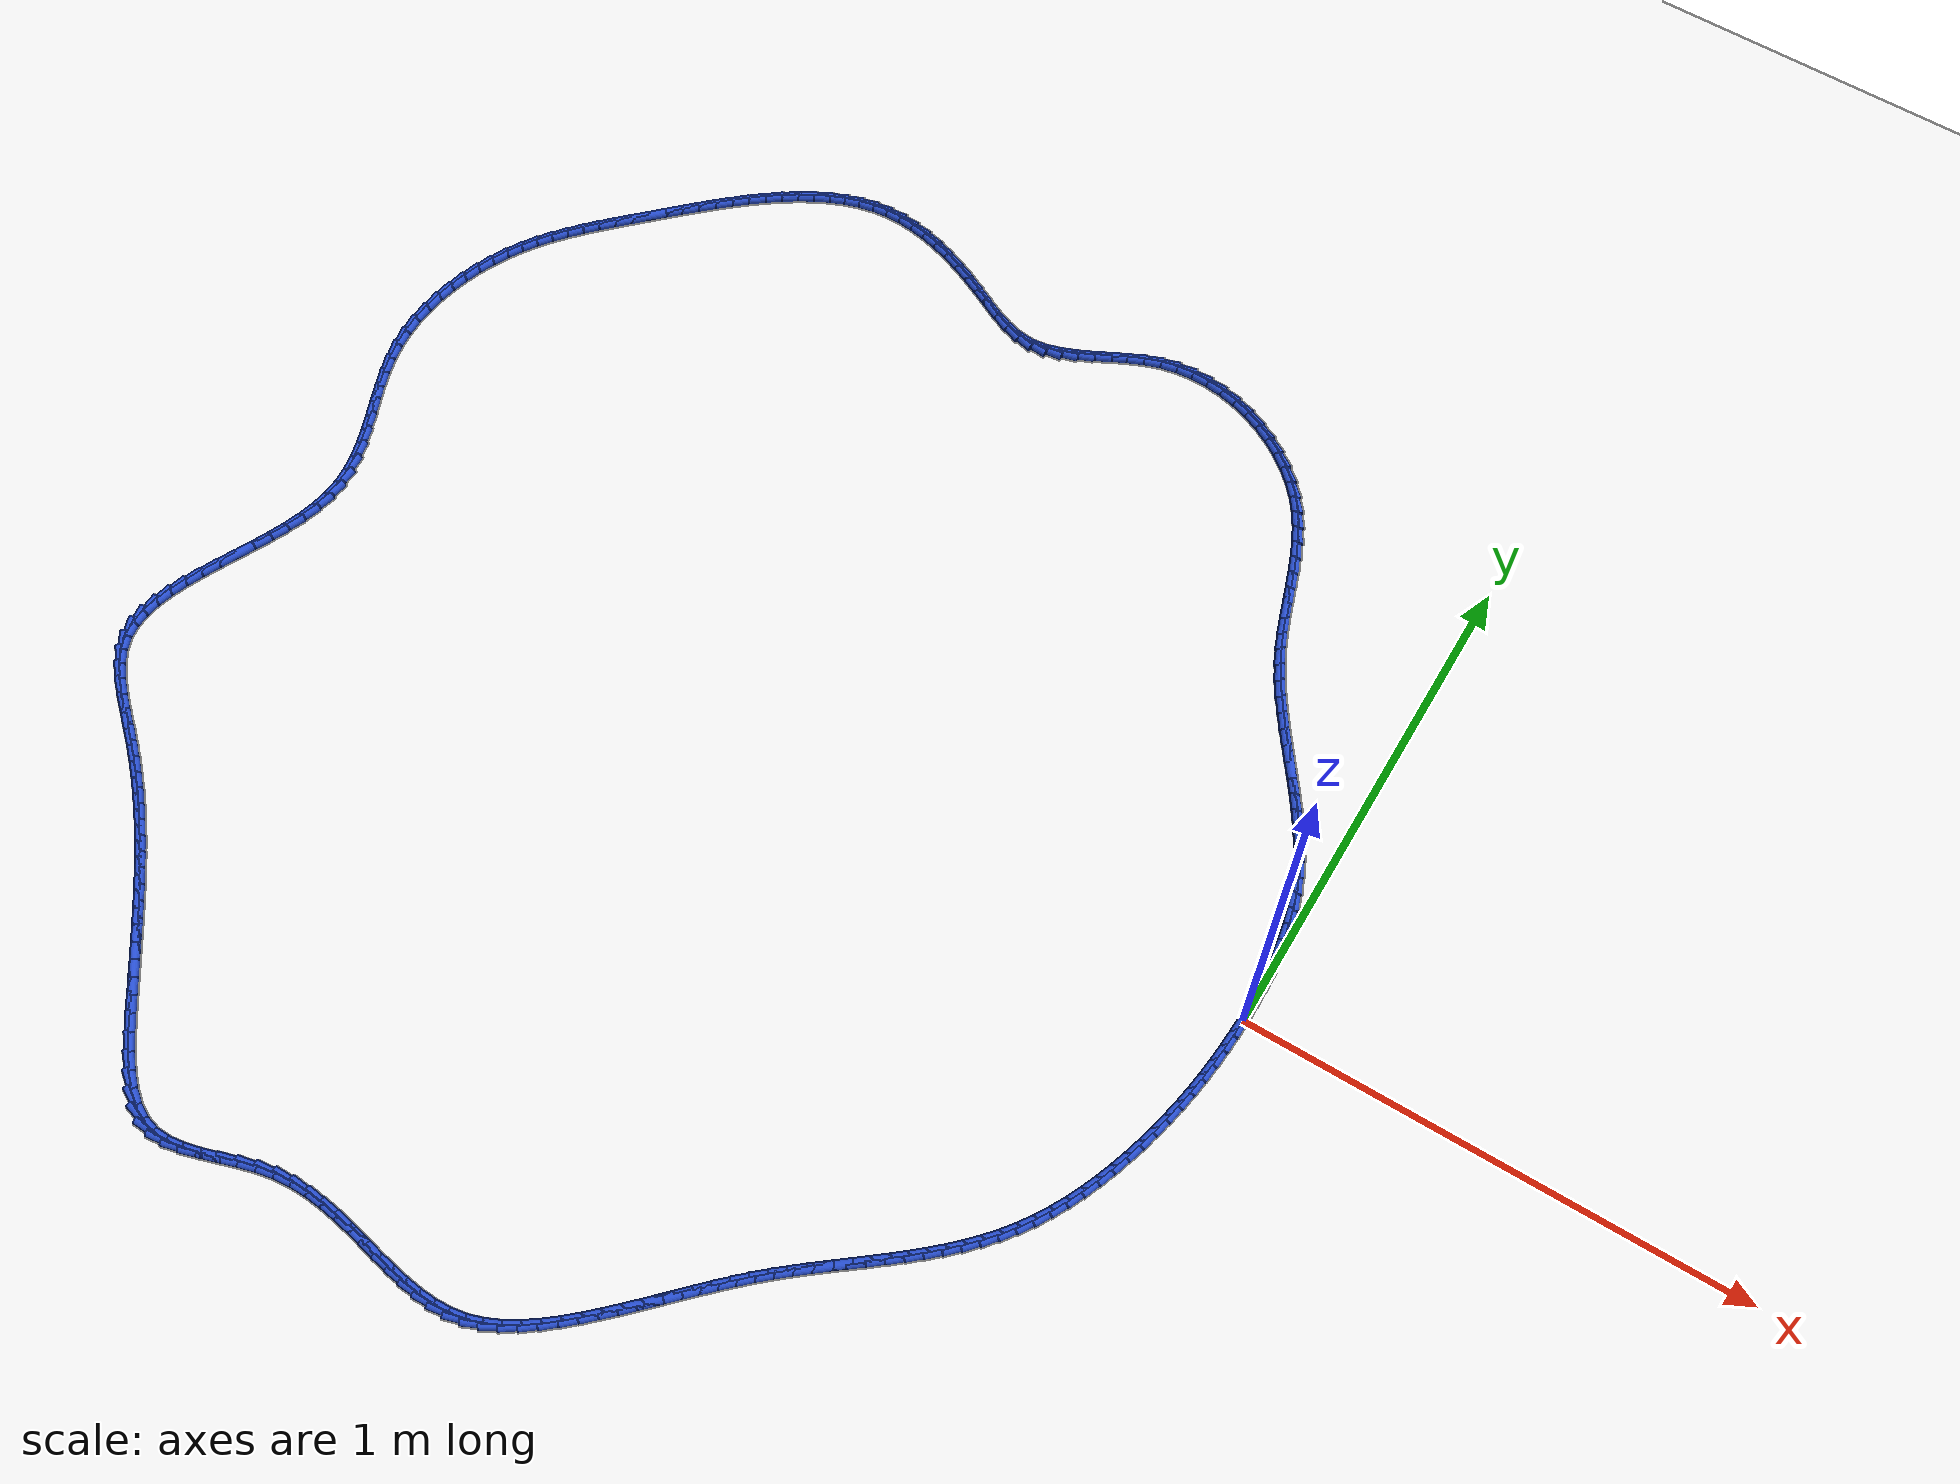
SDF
<sdf version="1.6">
 <world name="default">
  <light name="sun" type="directional">
   <pose>0 0 10 0 -0 0</pose>
   <diffuse>0.8 0.8 0.8 1</diffuse>
   <specular>0.2 0.2 0.2 1</specular>
   <attenuation>
    <range>1000</range>
    <constant>0.9</constant>
    <linear>0.01</linear>
    <quadratic>0.001</quadratic>
   </attenuation>
   <direction>-0.5 0.1 -0.9</direction>
  </light>
  <model name="ground_plane">
   <static>1</static>
   <link name="link">
    <collision name="collision">
     <geometry><plane><normal>0 0 1</normal><size>100 100</size></plane></geometry>
     <surface><friction><ode><mu>100</mu><mu2>50</mu2></ode></friction></surface>
    </collision>
    <visual name="visual">
     <cast_shadows>0</cast_shadows>
     <geometry><plane><normal>0 0 1</normal><size>100 100</size></plane></geometry>
     <material>
      <script><uri>file://media/materials/scripts/gazebo.material</uri><name>Gazebo/WhiteGlow</name></script>
     </material>
    </visual>
   </link>
  </model>
  <gravity>0 0 -9.8</gravity>
  <magnetic_field>6e-06 2.3e-05 -4.2e-05</magnetic_field>
  <atmosphere type="adiabatic"/>
  <physics name="default_physics" default="0" type="ode">
   <max_step_size>0.001</max_step_size>
   <real_time_factor>1</real_time_factor>
   <real_time_update_rate>1000</real_time_update_rate>
  </physics>
  <scene><ambient>0.4 0.4 0.4 1</ambient><background>0.7 0.7 0.7 1</background><shadows>1</shadows></scene>
  <spherical_coordinates>
   <surface_model>EARTH_WGS84</surface_model>
   <latitude_deg>0</latitude_deg>
   <longitude_deg>0</longitude_deg>
   <elevation>0</elevation>
   <heading_deg>0</heading_deg>
  </spherical_coordinates>
  <model name="line">
   <link name="link_0">
    <pose>9.107298248878237e-18 3.469446951953614e-17 0.01 0 1.57 1.5611285611488255</pose>
    <collision name="collision">
     <geometry><cylinder><radius>0.01</radius><length>0.08</length></cylinder></geometry>
    </collision>
    <visual name="visual">
     <material>
      <script><name>Gazebo/Blue</name><uri>file://media/materials/scripts/gazebo.material</uri></script>
     </material>
     <geometry><cylinder><radius>0.01</radius><length>0.08</length></cylinder></geometry>
    </visual>
   </link>
   <link name="link_1">
    <pose>0.00032561232508654137 0.03367915528946267 0.01 0 1.57 -1.5499684981782071</pose>
    <collision name="collision">
     <geometry><cylinder><radius>0.01</radius><length>0.08</length></cylinder></geometry>
    </collision>
    <visual name="visual">
     <material>
      <script><name>Gazebo/Blue</name><uri>file://media/materials/scripts/gazebo.material</uri></script>
     </material>
     <geometry><cylinder><radius>0.01</radius><length>0.08</length></cylinder></geometry>
    </visual>
   </link>
   <link name="link_2">
    <pose>-0.00037754978675397867 0.0674349752053072 0.01 0 1.57 -1.515329528181096</pose>
    <collision name="collision">
     <geometry><cylinder><radius>0.01</radius><length>0.08</length></cylinder></geometry>
    </collision>
    <visual name="visual">
     <material>
      <script><name>Gazebo/Blue</name><uri>file://media/materials/scripts/gazebo.material</uri></script>
     </material>
     <geometry><cylinder><radius>0.01</radius><length>0.08</length></cylinder></geometry>
    </visual>
   </link>
   <link name="link_3">
    <pose>-0.0022486380866745884 0.10113385653426568 0.01 0 1.57 -1.4762321920403072</pose>
    <collision name="collision">
     <geometry><cylinder><radius>0.01</radius><length>0.08</length></cylinder></geometry>
    </collision>
    <visual name="visual">
     <material>
      <script><name>Gazebo/Blue</name><uri>file://media/materials/scripts/gazebo.material</uri></script>
     </material>
     <geometry><cylinder><radius>0.01</radius><length>0.08</length></cylinder></geometry>
    </visual>
   </link>
   <link name="link_4">
    <pose>-0.00542680432582833 0.13464219606307032 0.01 0 1.57 -1.4323326726854175</pose>
    <collision name="collision">
     <geometry><cylinder><radius>0.01</radius><length>0.08</length></cylinder></geometry>
    </collision>
    <visual name="visual">
     <material>
      <script><name>Gazebo/Blue</name><uri>file://media/materials/scripts/gazebo.material</uri></script>
     </material>
     <geometry><cylinder><radius>0.01</radius><length>0.08</length></cylinder></geometry>
    </visual>
   </link>
   <link name="link_5">
    <pose>-0.010051200255368247 0.1678263905784531 0.01 0 1.57 -1.3832776218806389</pose>
    <collision name="collision">
     <geometry><cylinder><radius>0.01</radius><length>0.08</length></cylinder></geometry>
    </collision>
    <visual name="visual">
     <material>
      <script><name>Gazebo/Blue</name><uri>file://media/materials/scripts/gazebo.material</uri></script>
     </material>
     <geometry><cylinder><radius>0.01</radius><length>0.08</length></cylinder></geometry>
    </visual>
   </link>
   <link name="link_6">
    <pose>-0.016260977626447366 0.2005528368671461 0.01 0 1.57 -1.3287328669685963</pose>
    <collision name="collision">
     <geometry><cylinder><radius>0.01</radius><length>0.08</length></cylinder></geometry>
    </collision>
    <visual name="visual">
     <material>
      <script><name>Gazebo/Blue</name><uri>file://media/materials/scripts/gazebo.material</uri></script>
     </material>
     <geometry><cylinder><radius>0.01</radius><length>0.08</length></cylinder></geometry>
    </visual>
   </link>
   <link name="link_7">
    <pose>-0.02419528819021874 0.23268793171588148 0.01 0 1.57 -1.2684241439287702</pose>
    <collision name="collision">
     <geometry><cylinder><radius>0.01</radius><length>0.08</length></cylinder></geometry>
    </collision>
    <visual name="visual">
     <material>
      <script><name>Gazebo/Blue</name><uri>file://media/materials/scripts/gazebo.material</uri></script>
     </material>
     <geometry><cylinder><radius>0.01</radius><length>0.08</length></cylinder></geometry>
    </visual>
   </link>
   <link name="link_8">
    <pose>-0.0339932836978354 0.26409807191139123 0.01 0 1.57 -1.2023822367100183</pose>
    <collision name="collision">
     <geometry><cylinder><radius>0.01</radius><length>0.08</length></cylinder></geometry>
    </collision>
    <visual name="visual">
     <material>
      <script><name>Gazebo/Blue</name><uri>file://media/materials/scripts/gazebo.material</uri></script>
     </material>
     <geometry><cylinder><radius>0.01</radius><length>0.08</length></cylinder></geometry>
    </visual>
   </link>
   <link name="link_9">
    <pose>-0.04578873210994426 0.2946530786457331 0.01 0 1.57 -1.1371002337295038</pose>
    <collision name="collision">
     <geometry><cylinder><radius>0.01</radius><length>0.08</length></cylinder></geometry>
    </collision>
    <visual name="visual">
     <material>
      <script><name>Gazebo/Blue</name><uri>file://media/materials/scripts/gazebo.material</uri></script>
     </material>
     <geometry><cylinder><radius>0.01</radius><length>0.08</length></cylinder></geometry>
    </visual>
   </link>
   <link name="link_10">
    <pose>-0.059535509868876395 0.3243371946272946 0.01 0 1.57 -1.0808007374368802</pose>
    <collision name="collision">
     <geometry><cylinder><radius>0.01</radius><length>0.08</length></cylinder></geometry>
    </collision>
    <visual name="visual">
     <material>
      <script><name>Gazebo/Blue</name><uri>file://media/materials/scripts/gazebo.material</uri></script>
     </material>
     <geometry><cylinder><radius>0.01</radius><length>0.08</length></cylinder></geometry>
    </visual>
   </link>
   <link name="link_11">
    <pose>-0.0749695237020573 0.3532733040386539 0.01 0 1.57 -1.0342158421964478</pose>
    <collision name="collision">
     <geometry><cylinder><radius>0.01</radius><length>0.08</length></cylinder></geometry>
    </collision>
    <visual name="visual">
     <material>
      <script><name>Gazebo/Blue</name><uri>file://media/materials/scripts/gazebo.material</uri></script>
     </material>
     <geometry><cylinder><radius>0.01</radius><length>0.08</length></cylinder></geometry>
    </visual>
   </link>
   <link name="link_12">
    <pose>-0.09181359279044954 0.3815926155066173 0.01 0 1.57 -0.9973304996377963</pose>
    <collision name="collision">
     <geometry><cylinder><radius>0.01</radius><length>0.08</length></cylinder></geometry>
    </collision>
    <visual name="visual">
     <material>
      <script><name>Gazebo/Blue</name><uri>file://media/materials/scripts/gazebo.material</uri></script>
     </material>
     <geometry><cylinder><radius>0.01</radius><length>0.08</length></cylinder></geometry>
    </visual>
   </link>
   <link name="link_13">
    <pose>-0.1097905363150157 0.4094263376579907 0.01 0 1.57 -0.9699785528373828</pose>
    <collision name="collision">
     <geometry><cylinder><radius>0.01</radius><length>0.08</length></cylinder></geometry>
    </collision>
    <visual name="visual">
     <material>
      <script><name>Gazebo/Blue</name><uri>file://media/materials/scripts/gazebo.material</uri></script>
     </material>
     <geometry><cylinder><radius>0.01</radius><length>0.08</length></cylinder></geometry>
    </visual>
   </link>
   <link name="link_14">
    <pose>-0.1286231734567183 0.4369056791195802 0.01 0 1.57 -0.9519461760253578</pose>
    <collision name="collision">
     <geometry><cylinder><radius>0.01</radius><length>0.08</length></cylinder></geometry>
    </collision>
    <visual name="visual">
     <material>
      <script><name>Gazebo/Blue</name><uri>file://media/materials/scripts/gazebo.material</uri></script>
     </material>
     <geometry><cylinder><radius>0.01</radius><length>0.08</length></cylinder></geometry>
    </visual>
   </link>
   <link name="link_15">
    <pose>-0.14803432339652003 0.4641618485181921 0.01 0 1.57 -0.943043501567155</pose>
    <collision name="collision">
     <geometry><cylinder><radius>0.01</radius><length>0.08</length></cylinder></geometry>
    </collision>
    <visual name="visual">
     <material>
      <script><name>Gazebo/Blue</name><uri>file://media/materials/scripts/gazebo.material</uri></script>
     </material>
     <geometry><cylinder><radius>0.01</radius><length>0.08</length></cylinder></geometry>
    </visual>
   </link>
   <link name="link_16">
    <pose>-0.16774680531538338 0.49132605448063243 0.01 0 1.57 -0.9431477312933013</pose>
    <collision name="collision">
     <geometry><cylinder><radius>0.01</radius><length>0.08</length></cylinder></geometry>
    </collision>
    <visual name="visual">
     <material>
      <script><name>Gazebo/Blue</name><uri>file://media/materials/scripts/gazebo.material</uri></script>
     </material>
     <geometry><cylinder><radius>0.01</radius><length>0.08</length></cylinder></geometry>
    </visual>
   </link>
   <link name="link_17">
    <pose>-0.1874834383942709 0.5185295056337073 0.01 0 1.57 -0.9522224159867091</pose>
    <collision name="collision">
     <geometry><cylinder><radius>0.01</radius><length>0.08</length></cylinder></geometry>
    </collision>
    <visual name="visual">
     <material>
      <script><name>Gazebo/Blue</name><uri>file://media/materials/scripts/gazebo.material</uri></script>
     </material>
     <geometry><cylinder><radius>0.01</radius><length>0.08</length></cylinder></geometry>
    </visual>
   </link>
   <link name="link_18">
    <pose>-0.20696704181414527 0.5459034106042228 0.01 0 1.57 -0.9703160737288602</pose>
    <collision name="collision">
     <geometry><cylinder><radius>0.01</radius><length>0.08</length></cylinder></geometry>
    </collision>
    <visual name="visual">
     <material>
      <script><name>Gazebo/Blue</name><uri>file://media/materials/scripts/gazebo.material</uri></script>
     </material>
     <geometry><cylinder><radius>0.01</radius><length>0.08</length></cylinder></geometry>
    </visual>
   </link>
   <link name="link_19">
    <pose>-0.22592043475596893 0.573578978018985 0.01 0 1.57 -0.9975407189631754</pose>
    <collision name="collision">
     <geometry><cylinder><radius>0.01</radius><length>0.08</length></cylinder></geometry>
    </collision>
    <visual name="visual">
     <material>
      <script><name>Gazebo/Blue</name><uri>file://media/materials/scripts/gazebo.material</uri></script>
     </material>
     <geometry><cylinder><radius>0.01</radius><length>0.08</length></cylinder></geometry>
    </visual>
   </link>
   <link name="link_20">
    <pose>-0.24406643640070458 0.6016874165048003 0.01 0 1.57 -1.0340284078410977</pose>
    <collision name="collision">
     <geometry><cylinder><radius>0.01</radius><length>0.08</length></cylinder></geometry>
    </collision>
    <visual name="visual">
     <material>
      <script><name>Gazebo/Blue</name><uri>file://media/materials/scripts/gazebo.material</uri></script>
     </material>
     <geometry><cylinder><radius>0.01</radius><length>0.08</length></cylinder></geometry>
    </visual>
   </link>
   <link name="link_21">
    <pose>-0.26112786592931464 0.6303599346884744 0.01 0 1.57 -1.079862702196462</pose>
    <collision name="collision">
     <geometry><cylinder><radius>0.01</radius><length>0.08</length></cylinder></geometry>
    </collision>
    <visual name="visual">
     <material>
      <script><name>Gazebo/Blue</name><uri>file://media/materials/scripts/gazebo.material</uri></script>
     </material>
     <geometry><cylinder><radius>0.01</radius><length>0.08</length></cylinder></geometry>
    </visual>
   </link>
   <link name="link_22">
    <pose>-0.2768275425227618 0.6597277411968137 0.01 0 1.57 -1.1344654937425382</pose>
    <collision name="collision">
     <geometry><cylinder><radius>0.01</radius><length>0.08</length></cylinder></geometry>
    </collision>
    <visual name="visual">
     <material>
      <script><name>Gazebo/Blue</name><uri>file://media/materials/scripts/gazebo.material</uri></script>
     </material>
     <geometry><cylinder><radius>0.01</radius><length>0.08</length></cylinder></geometry>
    </visual>
   </link>
   <link name="link_23">
    <pose>-0.2909037059516896 0.6899142877210382 0.01 0 1.57 -1.1857438028348144</pose>
    <collision name="collision">
     <geometry><cylinder><radius>0.01</radius><length>0.08</length></cylinder></geometry>
    </collision>
    <visual name="visual">
     <material>
      <script><name>Gazebo/Blue</name><uri>file://media/materials/scripts/gazebo.material</uri></script>
     </material>
     <geometry><cylinder><radius>0.01</radius><length>0.08</length></cylinder></geometry>
    </visual>
   </link>
   <link name="link_24">
    <pose>-0.30344767789450816 0.7208654170754177 0.01 0 1.57 -1.2218448732244316</pose>
    <collision name="collision">
     <geometry><cylinder><radius>0.01</radius><length>0.08</length></cylinder></geometry>
    </collision>
    <visual name="visual">
     <material>
      <script><name>Gazebo/Blue</name><uri>file://media/materials/scripts/gazebo.material</uri></script>
     </material>
     <geometry><cylinder><radius>0.01</radius><length>0.08</length></cylinder></geometry>
    </visual>
   </link>
   <link name="link_25">
    <pose>-0.31490297994188227 0.7523498068626908 0.01 0 1.57 -1.2424753589264126</pose>
    <collision name="collision">
     <geometry><cylinder><radius>0.01</radius><length>0.08</length></cylinder></geometry>
    </collision>
    <visual name="visual">
     <material>
      <script><name>Gazebo/Blue</name><uri>file://media/materials/scripts/gazebo.material</uri></script>
     </material>
     <geometry><cylinder><radius>0.01</radius><length>0.08</length></cylinder></geometry>
    </visual>
   </link>
   <link name="link_26">
    <pose>-0.3257283778747088 0.7841284664832671 0.01 0 1.57 -1.2478320888802241</pose>
    <collision name="collision">
     <geometry><cylinder><radius>0.01</radius><length>0.08</length></cylinder></geometry>
    </collision>
    <visual name="visual">
     <material>
      <script><name>Gazebo/Blue</name><uri>file://media/materials/scripts/gazebo.material</uri></script>
     </material>
     <geometry><cylinder><radius>0.01</radius><length>0.08</length></cylinder></geometry>
    </visual>
   </link>
   <link name="link_27">
    <pose>-0.33638263747388486 0.8159624053375569 0.01 0 1.57 -1.2379459815192784</pose>
    <collision name="collision">
     <geometry><cylinder><radius>0.01</radius><length>0.08</length></cylinder></geometry>
    </collision>
    <visual name="visual">
     <material>
      <script><name>Gazebo/Blue</name><uri>file://media/materials/scripts/gazebo.material</uri></script>
     </material>
     <geometry><cylinder><radius>0.01</radius><length>0.08</length></cylinder></geometry>
    </visual>
   </link>
   <link name="link_28">
    <pose>-0.3473245245203075 0.8476126328259703 0.01 0 1.57 -1.2126446232018757</pose>
    <collision name="collision">
     <geometry><cylinder><radius>0.01</radius><length>0.08</length></cylinder></geometry>
    </collision>
    <visual name="visual">
     <material>
      <script><name>Gazebo/Blue</name><uri>file://media/materials/scripts/gazebo.material</uri></script>
     </material>
     <geometry><cylinder><radius>0.01</radius><length>0.08</length></cylinder></geometry>
    </visual>
   </link>
   <link name="link_29">
    <pose>-0.3590128047948737 0.8788401583489173 0.01 0 1.57 -1.1716178148179184</pose>
    <collision name="collision">
     <geometry><cylinder><radius>0.01</radius><length>0.08</length></cylinder></geometry>
    </collision>
    <visual name="visual">
     <material>
      <script><name>Gazebo/Blue</name><uri>file://media/materials/scripts/gazebo.material</uri></script>
     </material>
     <geometry><cylinder><radius>0.01</radius><length>0.08</length></cylinder></geometry>
    </visual>
   </link>
   <link name="link_30">
    <pose>-0.37190624407848044 0.909405991306808 0.01 0 1.57 -1.1145980190374123</pose>
    <collision name="collision">
     <geometry><cylinder><radius>0.01</radius><length>0.08</length></cylinder></geometry>
    </collision>
    <visual name="visual">
     <material>
      <script><name>Gazebo/Blue</name><uri>file://media/materials/scripts/gazebo.material</uri></script>
     </material>
     <geometry><cylinder><radius>0.01</radius><length>0.08</length></cylinder></geometry>
    </visual>
   </link>
   <link name="link_31">
    <pose>-0.38646360815202485 0.9390711411000523 0.01 0 1.57 -1.0416712162581887</pose>
    <collision name="collision">
     <geometry><cylinder><radius>0.01</radius><length>0.08</length></cylinder></geometry>
    </collision>
    <visual name="visual">
     <material>
      <script><name>Gazebo/Blue</name><uri>file://media/materials/scripts/gazebo.material</uri></script>
     </material>
     <geometry><cylinder><radius>0.01</radius><length>0.08</length></cylinder></geometry>
    </visual>
   </link>
   <link name="link_32">
    <pose>-0.4031436627964038 0.9675966171290603 0.01 0 1.57 -0.9537021575149164</pose>
    <collision name="collision">
     <geometry><cylinder><radius>0.01</radius><length>0.08</length></cylinder></geometry>
    </collision>
    <visual name="visual">
     <material>
      <script><name>Gazebo/Blue</name><uri>file://media/materials/scripts/gazebo.material</uri></script>
     </material>
     <geometry><cylinder><radius>0.01</radius><length>0.08</length></cylinder></geometry>
    </visual>
   </link>
   <link name="link_33">
    <pose>-0.4224051737925145 0.9947434287942423 0.01 0 1.57 -0.855158552038782</pose>
    <collision name="collision">
     <geometry><cylinder><radius>0.01</radius><length>0.08</length></cylinder></geometry>
    </collision>
    <visual name="visual">
     <material>
      <script><name>Gazebo/Blue</name><uri>file://media/materials/scripts/gazebo.material</uri></script>
     </material>
     <geometry><cylinder><radius>0.01</radius><length>0.08</length></cylinder></geometry>
    </visual>
   </link>
   <link name="link_34">
    <pose>-0.4446011126649982 1.0202742139274263 0.01 0 1.57 -0.7593038871052598</pose>
    <collision name="collision">
     <geometry><cylinder><radius>0.01</radius><length>0.08</length></cylinder></geometry>
    </collision>
    <visual name="visual">
     <material>
      <script><name>Gazebo/Blue</name><uri>file://media/materials/scripts/gazebo.material</uri></script>
     </material>
     <geometry><cylinder><radius>0.01</radius><length>0.08</length></cylinder></geometry>
    </visual>
   </link>
   <link name="link_35">
    <pose>-0.46955616965592606 1.043959741896773 0.01 0 1.57 -0.6683407710449254</pose>
    <collision name="collision">
     <geometry><cylinder><radius>0.01</radius><length>0.08</length></cylinder></geometry>
    </collision>
    <visual name="visual">
     <material>
      <script><name>Gazebo/Blue</name><uri>file://media/materials/scripts/gazebo.material</uri></script>
     </material>
     <geometry><cylinder><radius>0.01</radius><length>0.08</length></cylinder></geometry>
    </visual>
   </link>
   <link name="link_36">
    <pose>-0.49693047187999473 1.0655733150980042 0.01 0 1.57 -0.5804236306615369</pose>
    <collision name="collision">
     <geometry><cylinder><radius>0.01</radius><length>0.08</length></cylinder></geometry>
    </collision>
    <visual name="visual">
     <material>
      <script><name>Gazebo/Blue</name><uri>file://media/materials/scripts/gazebo.material</uri></script>
     </material>
     <geometry><cylinder><radius>0.01</radius><length>0.08</length></cylinder></geometry>
    </visual>
   </link>
   <link name="link_37">
    <pose>-0.526384093131403 1.0848882367475734 0.01 0 1.57 -0.49377571035946893</pose>
    <collision name="collision">
     <geometry><cylinder><radius>0.01</radius><length>0.08</length></cylinder></geometry>
    </collision>
    <visual name="visual">
     <material>
      <script><name>Gazebo/Blue</name><uri>file://media/materials/scripts/gazebo.material</uri></script>
     </material>
     <geometry><cylinder><radius>0.01</radius><length>0.08</length></cylinder></geometry>
    </visual>
   </link>
   <link name="link_38">
    <pose>-0.5575771072043505 1.1016778100619349 0.01 0 1.57 -0.406687297543019</pose>
    <collision name="collision">
     <geometry><cylinder><radius>0.01</radius><length>0.08</length></cylinder></geometry>
    </collision>
    <visual name="visual">
     <material>
      <script><name>Gazebo/Blue</name><uri>file://media/materials/scripts/gazebo.material</uri></script>
     </material>
     <geometry><cylinder><radius>0.01</radius><length>0.08</length></cylinder></geometry>
    </visual>
   </link>
   <link name="link_39">
    <pose>-0.5901695878930362 1.1157153382575424 0.01 0 1.57 -0.3175041588391482</pose>
    <collision name="collision">
     <geometry><cylinder><radius>0.01</radius><length>0.08</length></cylinder></geometry>
    </collision>
    <visual name="visual">
     <material>
      <script><name>Gazebo/Blue</name><uri>file://media/materials/scripts/gazebo.material</uri></script>
     </material>
     <geometry><cylinder><radius>0.01</radius><length>0.08</length></cylinder></geometry>
    </visual>
   </link>
   <link name="link_40">
    <pose>-0.6238216089916598 1.1267741245508505 0.01 0 1.57 -0.22462749539016788</pose>
    <collision name="collision">
     <geometry><cylinder><radius>0.01</radius><length>0.08</length></cylinder></geometry>
    </collision>
    <visual name="visual">
     <material>
      <script><name>Gazebo/Blue</name><uri>file://media/materials/scripts/gazebo.material</uri></script>
     </material>
     <geometry><cylinder><radius>0.01</radius><length>0.08</length></cylinder></geometry>
    </visual>
   </link>
   <link name="link_41">
    <pose>-0.65819324429442 1.1346274721583132 0.01 0 1.57 -0.1265444534481653</pose>
    <collision name="collision">
     <geometry><cylinder><radius>0.01</radius><length>0.08</length></cylinder></geometry>
    </collision>
    <visual name="visual">
     <material>
      <script><name>Gazebo/Blue</name><uri>file://media/materials/scripts/gazebo.material</uri></script>
     </material>
     <geometry><cylinder><radius>0.01</radius><length>0.08</length></cylinder></geometry>
    </visual>
   </link>
   <link name="link_42">
    <pose>-0.6929445675955168 1.1390486842963845 0.01 0 1.57 -0.021909575136972195</pose>
    <collision name="collision">
     <geometry><cylinder><radius>0.01</radius><length>0.08</length></cylinder></geometry>
    </collision>
    <visual name="visual">
     <material>
      <script><name>Gazebo/Blue</name><uri>file://media/materials/scripts/gazebo.material</uri></script>
     </material>
     <geometry><cylinder><radius>0.01</radius><length>0.08</length></cylinder></geometry>
    </visual>
   </link>
   <link name="link_43">
    <pose>-0.7277356526891489 1.1398110641815182 0.01 0 1.57 0.09030362127373852</pose>
    <collision name="collision">
     <geometry><cylinder><radius>0.01</radius><length>0.08</length></cylinder></geometry>
    </collision>
    <visual name="visual">
     <material>
      <script><name>Gazebo/Blue</name><uri>file://media/materials/scripts/gazebo.material</uri></script>
     </material>
     <geometry><cylinder><radius>0.01</radius><length>0.08</length></cylinder></geometry>
    </visual>
   </link>
   <link name="link_44">
    <pose>-0.7622265733695159 1.1366879150301683 0.01 0 1.57 0.2105340463668625</pose>
    <collision name="collision">
     <geometry><cylinder><radius>0.01</radius><length>0.08</length></cylinder></geometry>
    </collision>
    <visual name="visual">
     <material>
      <script><name>Gazebo/Blue</name><uri>file://media/materials/scripts/gazebo.material</uri></script>
     </material>
     <geometry><cylinder><radius>0.01</radius><length>0.08</length></cylinder></geometry>
    </visual>
   </link>
   <link name="link_45">
    <pose>-0.7960778137168979 1.1294538773477591 0.01 0 1.57 0.3262258473721855</pose>
    <collision name="collision">
     <geometry><cylinder><radius>0.01</radius><length>0.08</length></cylinder></geometry>
    </collision>
    <visual name="visual">
     <material>
      <script><name>Gazebo/Blue</name><uri>file://media/materials/scripts/gazebo.material</uri></script>
     </material>
     <geometry><cylinder><radius>0.01</radius><length>0.08</length></cylinder></geometry>
    </visual>
   </link>
   <link name="link_46">
    <pose>-0.8290747242917752 1.118290582211539 0.01 0 1.57 0.40806243210691506</pose>
    <collision name="collision">
     <geometry><cylinder><radius>0.01</radius><length>0.08</length></cylinder></geometry>
    </collision>
    <visual name="visual">
     <material>
      <script><name>Gazebo/Blue</name><uri>file://media/materials/scripts/gazebo.material</uri></script>
     </material>
     <geometry><cylinder><radius>0.01</radius><length>0.08</length></cylinder></geometry>
    </visual>
   </link>
   <link name="link_47">
    <pose>-0.8613026590067666 1.1043574934657228 0.01 0 1.57 0.45360297334405425</pose>
    <collision name="collision">
     <geometry><cylinder><radius>0.01</radius><length>0.08</length></cylinder></geometry>
    </collision>
    <visual name="visual">
     <material>
      <script><name>Gazebo/Blue</name><uri>file://media/materials/scripts/gazebo.material</uri></script>
     </material>
     <geometry><cylinder><radius>0.01</radius><length>0.08</length></cylinder></geometry>
    </visual>
   </link>
   <link name="link_48">
    <pose>-0.8928911041101981 1.0889579201603576 0.01 0 1.57 0.46425306585119125</pose>
    <collision name="collision">
     <geometry><cylinder><radius>0.01</radius><length>0.08</length></cylinder></geometry>
    </collision>
    <visual name="visual">
     <material>
      <script><name>Gazebo/Blue</name><uri>file://media/materials/scripts/gazebo.material</uri></script>
     </material>
     <geometry><cylinder><radius>0.01</radius><length>0.08</length></cylinder></geometry>
    </visual>
   </link>
   <link name="link_49">
    <pose>-0.9239695458503967 1.0733951713454921 0.01 0 1.57 0.43921654905221685</pose>
    <collision name="collision">
     <geometry><cylinder><radius>0.01</radius><length>0.08</length></cylinder></geometry>
    </collision>
    <visual name="visual">
     <material>
      <script><name>Gazebo/Blue</name><uri>file://media/materials/scripts/gazebo.material</uri></script>
     </material>
     <geometry><cylinder><radius>0.01</radius><length>0.08</length></cylinder></geometry>
    </visual>
   </link>
   <link name="link_50">
    <pose>-0.9546674704756897 1.0589725560711736 0.01 0 1.57 0.3748426192967173</pose>
    <collision name="collision">
     <geometry><cylinder><radius>0.01</radius><length>0.08</length></cylinder></geometry>
    </collision>
    <visual name="visual">
     <material>
      <script><name>Gazebo/Blue</name><uri>file://media/materials/scripts/gazebo.material</uri></script>
     </material>
     <geometry><cylinder><radius>0.01</radius><length>0.08</length></cylinder></geometry>
    </visual>
   </link>
   <link name="link_51">
    <pose>-0.9851143642344034 1.0469933833874498 0.01 0 1.57 0.2650813996110888</pose>
    <collision name="collision">
     <geometry><cylinder><radius>0.01</radius><length>0.08</length></cylinder></geometry>
    </collision>
    <visual name="visual">
     <material>
      <script><name>Gazebo/Blue</name><uri>file://media/materials/scripts/gazebo.material</uri></script>
     </material>
     <geometry><cylinder><radius>0.01</radius><length>0.08</length></cylinder></geometry>
    </visual>
   </link>
   <link name="link_52">
    <pose>-1.015439713374865 1.0387609623443688 0.01 0 1.57 0.10453073006149202</pose>
    <collision name="collision">
     <geometry><cylinder><radius>0.01</radius><length>0.08</length></cylinder></geometry>
    </collision>
    <visual name="visual">
     <material>
      <script><name>Gazebo/Blue</name><uri>file://media/materials/scripts/gazebo.material</uri></script>
     </material>
     <geometry><cylinder><radius>0.01</radius><length>0.08</length></cylinder></geometry>
    </visual>
   </link>
   <link name="link_53">
    <pose>-1.045773004145401 1.0355786019919782 0.01 0 1.57 -0.0980037029495043</pose>
    <collision name="collision">
     <geometry><cylinder><radius>0.01</radius><length>0.08</length></cylinder></geometry>
    </collision>
    <visual name="visual">
     <material>
      <script><name>Gazebo/Blue</name><uri>file://media/materials/scripts/gazebo.material</uri></script>
     </material>
     <geometry><cylinder><radius>0.01</radius><length>0.08</length></cylinder></geometry>
    </visual>
   </link>
   <link name="link_54">
    <pose>-1.076238483475714 1.0385739276852177 0.01 0 1.57 -0.2726589383385615</pose>
    <collision name="collision">
     <geometry><cylinder><radius>0.01</radius><length>0.08</length></cylinder></geometry>
    </collision>
    <visual name="visual">
     <material>
      <script><name>Gazebo/Blue</name><uri>file://media/materials/scripts/gazebo.material</uri></script>
     </material>
     <geometry><cylinder><radius>0.01</radius><length>0.08</length></cylinder></geometry>
    </visual>
   </link>
   <link name="link_55">
    <pose>-1.1069089704277046 1.0471500966765146 0.01 0 1.57 -0.3864689399810695</pose>
    <collision name="collision">
     <geometry><cylinder><radius>0.01</radius><length>0.08</length></cylinder></geometry>
    </collision>
    <visual name="visual">
     <material>
      <script><name>Gazebo/Blue</name><uri>file://media/materials/scripts/gazebo.material</uri></script>
     </material>
     <geometry><cylinder><radius>0.01</radius><length>0.08</length></cylinder></geometry>
    </visual>
   </link>
   <link name="link_56">
    <pose>-1.1378281134096322 1.0597321221908444 0.01 0 1.57 -0.4480499489922257</pose>
    <collision name="collision">
     <geometry><cylinder><radius>0.01</radius><length>0.08</length></cylinder></geometry>
    </collision>
    <visual name="visual">
     <material>
      <script><name>Gazebo/Blue</name><uri>file://media/materials/scripts/gazebo.material</uri></script>
     </material>
     <geometry><cylinder><radius>0.01</radius><length>0.08</length></cylinder></geometry>
    </visual>
   </link>
   <link name="link_57">
    <pose>-1.1690392267121268 1.0747338138933213 0.01 0 1.57 -0.46521786484681343</pose>
    <collision name="collision">
     <geometry><cylinder><radius>0.01</radius><length>0.08</length></cylinder></geometry>
    </collision>
    <visual name="visual">
     <material>
      <script><name>Gazebo/Blue</name><uri>file://media/materials/scripts/gazebo.material</uri></script>
     </material>
     <geometry><cylinder><radius>0.01</radius><length>0.08</length></cylinder></geometry>
    </visual>
   </link>
   <link name="link_58">
    <pose>-1.2005856246258162 1.090568981449056 0.01 0 1.57 -0.44412983115732446</pose>
    <collision name="collision">
     <geometry><cylinder><radius>0.01</radius><length>0.08</length></cylinder></geometry>
    </collision>
    <visual name="visual">
     <material>
      <script><name>Gazebo/Blue</name><uri>file://media/materials/scripts/gazebo.material</uri></script>
     </material>
     <geometry><cylinder><radius>0.01</radius><length>0.08</length></cylinder></geometry>
    </visual>
   </link>
   <link name="link_59">
    <pose>-1.2324981842894882 1.1057541111132307 0.01 0 1.57 -0.40635541657158475</pose>
    <collision name="collision">
     <geometry><cylinder><radius>0.01</radius><length>0.08</length></cylinder></geometry>
    </collision>
    <visual name="visual">
     <material>
      <script><name>Gazebo/Blue</name><uri>file://media/materials/scripts/gazebo.material</uri></script>
     </material>
     <geometry><cylinder><radius>0.01</radius><length>0.08</length></cylinder></geometry>
    </visual>
   </link>
   <link name="link_60">
    <pose>-1.2647097620148748 1.119614913343265 0.01 0 1.57 -0.3613849267755436</pose>
    <collision name="collision">
     <geometry><cylinder><radius>0.01</radius><length>0.08</length></cylinder></geometry>
    </collision>
    <visual name="visual">
     <material>
      <script><name>Gazebo/Blue</name><uri>file://media/materials/scripts/gazebo.material</uri></script>
     </material>
     <geometry><cylinder><radius>0.01</radius><length>0.08</length></cylinder></geometry>
    </visual>
   </link>
   <link name="link_61">
    <pose>-1.2971067739045594 1.1318604920276625 0.01 0 1.57 -0.30835606208274874</pose>
    <collision name="collision">
     <geometry><cylinder><radius>0.01</radius><length>0.08</length></cylinder></geometry>
    </collision>
    <visual name="visual">
     <material>
      <script><name>Gazebo/Blue</name><uri>file://media/materials/scripts/gazebo.material</uri></script>
     </material>
     <geometry><cylinder><radius>0.01</radius><length>0.08</length></cylinder></geometry>
    </visual>
   </link>
   <link name="link_62">
    <pose>-1.3295753575808298 1.142202250086674 0.01 0 1.57 -0.24621959633397472</pose>
    <collision name="collision">
     <geometry><cylinder><radius>0.01</radius><length>0.08</length></cylinder></geometry>
    </collision>
    <visual name="visual">
     <material>
      <script><name>Gazebo/Blue</name><uri>file://media/materials/scripts/gazebo.material</uri></script>
     </material>
     <geometry><cylinder><radius>0.01</radius><length>0.08</length></cylinder></geometry>
    </visual>
   </link>
   <link name="link_63">
    <pose>-1.3620016506659742 1.1503515904405508 0.01 0 1.57 -0.17387855035536814</pose>
    <collision name="collision">
     <geometry><cylinder><radius>0.01</radius><length>0.08</length></cylinder></geometry>
    </collision>
    <visual name="visual">
     <material>
      <script><name>Gazebo/Blue</name><uri>file://media/materials/scripts/gazebo.material</uri></script>
     </material>
     <geometry><cylinder><radius>0.01</radius><length>0.08</length></cylinder></geometry>
    </visual>
   </link>
   <link name="link_64">
    <pose>-1.3942717907822815 1.1560199160095441 0.01 0 1.57 -0.09033789793591095</pose>
    <collision name="collision">
     <geometry><cylinder><radius>0.01</radius><length>0.08</length></cylinder></geometry>
    </collision>
    <visual name="visual">
     <material>
      <script><name>Gazebo/Blue</name><uri>file://media/materials/scripts/gazebo.material</uri></script>
     </material>
     <geometry><cylinder><radius>0.01</radius><length>0.08</length></cylinder></geometry>
    </visual>
   </link>
   <link name="link_65">
    <pose>-1.4262719155520402 1.1589186297139054 0.01 0 1.57 0.005044681198250452</pose>
    <collision name="collision">
     <geometry><cylinder><radius>0.01</radius><length>0.08</length></cylinder></geometry>
    </collision>
    <visual name="visual">
     <material>
      <script><name>Gazebo/Blue</name><uri>file://media/materials/scripts/gazebo.material</uri></script>
     </material>
     <geometry><cylinder><radius>0.01</radius><length>0.08</length></cylinder></geometry>
    </visual>
   </link>
   <link name="link_66">
    <pose>-1.4578881625975397 1.1587591344738855 0.01 0 1.57 0.10991743101642538</pose>
    <collision name="collision">
     <geometry><cylinder><radius>0.01</radius><length>0.08</length></cylinder></geometry>
    </collision>
    <visual name="visual">
     <material>
      <script><name>Gazebo/Blue</name><uri>file://media/materials/scripts/gazebo.material</uri></script>
     </material>
     <geometry><cylinder><radius>0.01</radius><length>0.08</length></cylinder></geometry>
    </visual>
   </link>
   <link name="link_67">
    <pose>-1.4890230127385096 1.1553230223850424 0.01 0 1.57 0.21133307052214542</pose>
    <collision name="collision">
     <geometry><cylinder><radius>0.01</radius><length>0.08</length></cylinder></geometry>
    </collision>
    <visual name="visual">
     <material>
      <script><name>Gazebo/Blue</name><uri>file://media/materials/scripts/gazebo.material</uri></script>
     </material>
     <geometry><cylinder><radius>0.01</radius><length>0.08</length></cylinder></geometry>
    </visual>
   </link>
   <link name="link_68">
    <pose>-1.5196622811457638 1.1487497818112464 0.01 0 1.57 0.30389209584032767</pose>
    <collision name="collision">
     <geometry><cylinder><radius>0.01</radius><length>0.08</length></cylinder></geometry>
    </collision>
    <visual name="visual">
     <material>
      <script><name>Gazebo/Blue</name><uri>file://media/materials/scripts/gazebo.material</uri></script>
     </material>
     <geometry><cylinder><radius>0.01</radius><length>0.08</length></cylinder></geometry>
    </visual>
   </link>
   <link name="link_69">
    <pose>-1.5498182764425432 1.1392926826198766 0.01 0 1.57 0.3866946898808996</pose>
    <collision name="collision">
     <geometry><cylinder><radius>0.01</radius><length>0.08</length></cylinder></geometry>
    </collision>
    <visual name="visual">
     <material>
      <script><name>Gazebo/Blue</name><uri>file://media/materials/scripts/gazebo.material</uri></script>
     </material>
     <geometry><cylinder><radius>0.01</radius><length>0.08</length></cylinder></geometry>
    </visual>
   </link>
   <link name="link_70">
    <pose>-1.5795033182702796 1.1272050419981534 0.01 0 1.57 0.4595789574771931</pose>
    <collision name="collision">
     <geometry><cylinder><radius>0.01</radius><length>0.08</length></cylinder></geometry>
    </collision>
    <visual name="visual">
     <material>
      <script><name>Gazebo/Blue</name><uri>file://media/materials/scripts/gazebo.material</uri></script>
     </material>
     <geometry><cylinder><radius>0.01</radius><length>0.08</length></cylinder></geometry>
    </visual>
   </link>
   <link name="link_71">
    <pose>-1.6087297262704041 1.1127401771332988 0.01 0 1.57 0.5228838464333658</pose>
    <collision name="collision">
     <geometry><cylinder><radius>0.01</radius><length>0.08</length></cylinder></geometry>
    </collision>
    <visual name="visual">
     <material>
      <script><name>Gazebo/Blue</name><uri>file://media/materials/scripts/gazebo.material</uri></script>
     </material>
     <geometry><cylinder><radius>0.01</radius><length>0.08</length></cylinder></geometry>
    </visual>
   </link>
   <link name="link_72">
    <pose>-1.6375098200843476 1.0961514052125327 0.01 0 1.57 0.5772278051789631</pose>
    <collision name="collision">
     <geometry><cylinder><radius>0.01</radius><length>0.08</length></cylinder></geometry>
    </collision>
    <visual name="visual">
     <material>
      <script><name>Gazebo/Blue</name><uri>file://media/materials/scripts/gazebo.material</uri></script>
     </material>
     <geometry><cylinder><radius>0.01</radius><length>0.08</length></cylinder></geometry>
    </visual>
   </link>
   <link name="link_73">
    <pose>-1.6658559193535403 1.0776920434230772 0.01 0 1.57 0.6233399161092285</pose>
    <collision name="collision">
     <geometry><cylinder><radius>0.01</radius><length>0.08</length></cylinder></geometry>
    </collision>
    <visual name="visual">
     <material>
      <script><name>Gazebo/Blue</name><uri>file://media/materials/scripts/gazebo.material</uri></script>
     </material>
     <geometry><cylinder><radius>0.01</radius><length>0.08</length></cylinder></geometry>
    </visual>
   </link>
   <link name="link_74">
    <pose>-1.6937803437194137 1.0576154089521526 0.01 0 1.57 0.6619478909796318</pose>
    <collision name="collision">
     <geometry><cylinder><radius>0.01</radius><length>0.08</length></cylinder></geometry>
    </collision>
    <visual name="visual">
     <material>
      <script><name>Gazebo/Blue</name><uri>file://media/materials/scripts/gazebo.material</uri></script>
     </material>
     <geometry><cylinder><radius>0.01</radius><length>0.08</length></cylinder></geometry>
    </visual>
   </link>
   <link name="link_75">
    <pose>-1.7212954128233988 1.0361748189869808 0.01 0 1.57 0.6937116544467744</pose>
    <collision name="collision">
     <geometry><cylinder><radius>0.01</radius><length>0.08</length></cylinder></geometry>
    </collision>
    <visual name="visual">
     <material>
      <script><name>Gazebo/Blue</name><uri>file://media/materials/scripts/gazebo.material</uri></script>
     </material>
     <geometry><cylinder><radius>0.01</radius><length>0.08</length></cylinder></geometry>
    </visual>
   </link>
   <link name="link_76">
    <pose>-1.7484134463069263 1.0136235907147826 0.01 0 1.57 0.7191878581240776</pose>
    <collision name="collision">
     <geometry><cylinder><radius>0.01</radius><length>0.08</length></cylinder></geometry>
    </collision>
    <visual name="visual">
     <material>
      <script><name>Gazebo/Blue</name><uri>file://media/materials/scripts/gazebo.material</uri></script>
     </material>
     <geometry><cylinder><radius>0.01</radius><length>0.08</length></cylinder></geometry>
    </visual>
   </link>
   <link name="link_77">
    <pose>-1.7751467638114269 0.9902150413227793 0.01 0 1.57 0.7388127568755634</pose>
    <collision name="collision">
     <geometry><cylinder><radius>0.01</radius><length>0.08</length></cylinder></geometry>
    </collision>
    <visual name="visual">
     <material>
      <script><name>Gazebo/Blue</name><uri>file://media/materials/scripts/gazebo.material</uri></script>
     </material>
     <geometry><cylinder><radius>0.01</radius><length>0.08</length></cylinder></geometry>
    </visual>
   </link>
   <link name="link_78">
    <pose>-1.8015076849783318 0.966202487998191 0.01 0 1.57 0.7528942935353788</pose>
    <collision name="collision">
     <geometry><cylinder><radius>0.01</radius><length>0.08</length></cylinder></geometry>
    </collision>
    <visual name="visual">
     <material>
      <script><name>Gazebo/Blue</name><uri>file://media/materials/scripts/gazebo.material</uri></script>
     </material>
     <geometry><cylinder><radius>0.01</radius><length>0.08</length></cylinder></geometry>
    </visual>
   </link>
   <link name="link_79">
    <pose>-1.8275085294490718 0.9418392479282401 0.01 0 1.57 0.7616072067306237</pose>
    <collision name="collision">
     <geometry><cylinder><radius>0.01</radius><length>0.08</length></cylinder></geometry>
    </collision>
    <visual name="visual">
     <material>
      <script><name>Gazebo/Blue</name><uri>file://media/materials/scripts/gazebo.material</uri></script>
     </material>
     <geometry><cylinder><radius>0.01</radius><length>0.08</length></cylinder></geometry>
    </visual>
   </link>
   <link name="link_80">
    <pose>-1.8531616168650784 0.917378638300147 0.01 0 1.57 0.7649870361466131</pose>
    <collision name="collision">
     <geometry><cylinder><radius>0.01</radius><length>0.08</length></cylinder></geometry>
    </collision>
    <visual name="visual">
     <material>
      <script><name>Gazebo/Blue</name><uri>file://media/materials/scripts/gazebo.material</uri></script>
     </material>
     <geometry><cylinder><radius>0.01</radius><length>0.08</length></cylinder></geometry>
    </visual>
   </link>
   <link name="link_81">
    <pose>-1.8784792668677812 0.8930739763011329 0.01 0 1.57 0.764797828318184</pose>
    <collision name="collision">
     <geometry><cylinder><radius>0.01</radius><length>0.08</length></cylinder></geometry>
    </collision>
    <visual name="visual">
     <material>
      <script><name>Gazebo/Blue</name><uri>file://media/materials/scripts/gazebo.material</uri></script>
     </material>
     <geometry><cylinder><radius>0.01</radius><length>0.08</length></cylinder></geometry>
    </visual>
   </link>
   <link name="link_82">
    <pose>-1.9034504246843378 0.869111020249248 0.01 0 1.57 0.7696742958405746</pose>
    <collision name="collision">
     <geometry><cylinder><radius>0.01</radius><length>0.08</length></cylinder></geometry>
    </collision>
    <visual name="visual">
     <material>
      <script><name>Gazebo/Blue</name><uri>file://media/materials/scripts/gazebo.material</uri></script>
     </material>
     <geometry><cylinder><radius>0.01</radius><length>0.08</length></cylinder></geometry>
    </visual>
   </link>
   <link name="link_83">
    <pose>-1.9279562454174448 0.8453639835899778 0.01 0 1.57 0.7823766001321093</pose>
    <collision name="collision">
     <geometry><cylinder><radius>0.01</radius><length>0.08</length></cylinder></geometry>
    </collision>
    <visual name="visual">
     <material>
      <script><name>Gazebo/Blue</name><uri>file://media/materials/scripts/gazebo.material</uri></script>
     </material>
     <geometry><cylinder><radius>0.01</radius><length>0.08</length></cylinder></geometry>
    </visual>
   </link>
   <link name="link_84">
    <pose>-1.9518468336509018 0.8216173347202622 0.01 0 1.57 0.8031578638252724</pose>
    <collision name="collision">
     <geometry><cylinder><radius>0.01</radius><length>0.08</length></cylinder></geometry>
    </collision>
    <visual name="visual">
     <material>
      <script><name>Gazebo/Blue</name><uri>file://media/materials/scripts/gazebo.material</uri></script>
     </material>
     <geometry><cylinder><radius>0.01</radius><length>0.08</length></cylinder></geometry>
    </visual>
   </link>
   <link name="link_85">
    <pose>-1.974972291097411 0.7976555337387308 0.01 0 1.57 0.8321864770874734</pose>
    <collision name="collision">
     <geometry><cylinder><radius>0.01</radius><length>0.08</length></cylinder></geometry>
    </collision>
    <visual name="visual">
     <material>
      <script><name>Gazebo/Blue</name><uri>file://media/materials/scripts/gazebo.material</uri></script>
     </material>
     <geometry><cylinder><radius>0.01</radius><length>0.08</length></cylinder></geometry>
    </visual>
   </link>
   <link name="link_86">
    <pose>-1.9971827194696754 0.7732630407440149 0.01 0 1.57 0.8694970317864423</pose>
    <collision name="collision">
     <geometry><cylinder><radius>0.01</radius><length>0.08</length></cylinder></geometry>
    </collision>
    <visual name="visual">
     <material>
      <script><name>Gazebo/Blue</name><uri>file://media/materials/scripts/gazebo.material</uri></script>
     </material>
     <geometry><cylinder><radius>0.01</radius><length>0.08</length></cylinder></geometry>
    </visual>
   </link>
   <link name="link_87">
    <pose>-2.0183282204803983 0.7482243158347444 0.01 0 1.57 0.9149256816366125</pose>
    <collision name="collision">
     <geometry><cylinder><radius>0.01</radius><length>0.08</length></cylinder></geometry>
    </collision>
    <visual name="visual">
     <material>
      <script><name>Gazebo/Blue</name><uri>file://media/materials/scripts/gazebo.material</uri></script>
     </material>
     <geometry><cylinder><radius>0.01</radius><length>0.08</length></cylinder></geometry>
    </visual>
   </link>
   <link name="link_88">
    <pose>-2.0382588958422803 0.7223238191095496 0.01 0 1.57 0.9680382402038945</pose>
    <collision name="collision">
     <geometry><cylinder><radius>0.01</radius><length>0.08</length></cylinder></geometry>
    </collision>
    <visual name="visual">
     <material>
      <script><name>Gazebo/Blue</name><uri>file://media/materials/scripts/gazebo.material</uri></script>
     </material>
     <geometry><cylinder><radius>0.01</radius><length>0.08</length></cylinder></geometry>
    </visual>
   </link>
   <link name="link_89">
    <pose>-2.0568248472680253 0.695346010667061 0.01 0 1.57 1.0280625030085169</pose>
    <collision name="collision">
     <geometry><cylinder><radius>0.01</radius><length>0.08</length></cylinder></geometry>
    </collision>
    <visual name="visual">
     <material>
      <script><name>Gazebo/Blue</name><uri>file://media/materials/scripts/gazebo.material</uri></script>
     </material>
     <geometry><cylinder><radius>0.01</radius><length>0.08</length></cylinder></geometry>
    </visual>
   </link>
   <link name="link_90">
    <pose>-2.073876177714001 0.6670756338138539 0.01 0 1.57 1.0923530774912777</pose>
    <collision name="collision">
     <geometry><cylinder><radius>0.01</radius><length>0.08</length></cylinder></geometry>
    </collision>
    <visual name="visual">
     <material>
      <script><name>Gazebo/Blue</name><uri>file://media/materials/scripts/gazebo.material</uri></script>
     </material>
     <geometry><cylinder><radius>0.01</radius><length>0.08</length></cylinder></geometry>
    </visual>
   </link>
   <link name="link_91">
    <pose>-2.089263470125698 0.6374067352211935 0.01 0 1.57 1.1568482342730044</pose>
    <collision name="collision">
     <geometry><cylinder><radius>0.01</radius><length>0.08</length></cylinder></geometry>
    </collision>
    <visual name="visual">
     <material>
      <script><name>Gazebo/Blue</name><uri>file://media/materials/scripts/gazebo.material</uri></script>
     </material>
     <geometry><cylinder><radius>0.01</radius><length>0.08</length></cylinder></geometry>
    </visual>
   </link>
   <link name="link_92">
    <pose>-2.102838511471747 0.6065075423157977 0.01 0 1.57 1.2218075934569517</pose>
    <collision name="collision">
     <geometry><cylinder><radius>0.01</radius><length>0.08</length></cylinder></geometry>
    </collision>
    <visual name="visual">
     <material>
      <script><name>Gazebo/Blue</name><uri>file://media/materials/scripts/gazebo.material</uri></script>
     </material>
     <geometry><cylinder><radius>0.01</radius><length>0.08</length></cylinder></geometry>
    </visual>
   </link>
   <link name="link_93">
    <pose>-2.114453274483946 0.5745885846058175 0.01 0 1.57 1.2881082606237912</pose>
    <collision name="collision">
     <geometry><cylinder><radius>0.01</radius><length>0.08</length></cylinder></geometry>
    </collision>
    <visual name="visual">
     <material>
      <script><name>Gazebo/Blue</name><uri>file://media/materials/scripts/gazebo.material</uri></script>
     </material>
     <geometry><cylinder><radius>0.01</radius><length>0.08</length></cylinder></geometry>
    </visual>
   </link>
   <link name="link_94">
    <pose>-2.1239597318940926 0.5418603915994057 0.01 0 1.57 1.3565881906018822</pose>
    <collision name="collision">
     <geometry><cylinder><radius>0.01</radius><length>0.08</length></cylinder></geometry>
    </collision>
    <visual name="visual">
     <material>
      <script><name>Gazebo/Blue</name><uri>file://media/materials/scripts/gazebo.material</uri></script>
     </material>
     <geometry><cylinder><radius>0.01</radius><length>0.08</length></cylinder></geometry>
    </visual>
   </link>
   <link name="link_95">
    <pose>-2.131209856433984 0.5085334928047134 0.01 0 1.57 1.4280469799502449</pose>
    <collision name="collision">
     <geometry><cylinder><radius>0.01</radius><length>0.08</length></cylinder></geometry>
    </collision>
    <visual name="visual">
     <material>
      <script><name>Gazebo/Blue</name><uri>file://media/materials/scripts/gazebo.material</uri></script>
     </material>
     <geometry><cylinder><radius>0.01</radius><length>0.08</length></cylinder></geometry>
    </visual>
   </link>
   <link name="link_96">
    <pose>-2.136055620835418 0.47481841772989336 0.01 0 1.57 1.5032335504921208</pose>
    <collision name="collision">
     <geometry><cylinder><radius>0.01</radius><length>0.08</length></cylinder></geometry>
    </collision>
    <visual name="visual">
     <material>
      <script><name>Gazebo/Blue</name><uri>file://media/materials/scripts/gazebo.material</uri></script>
     </material>
     <geometry><cylinder><radius>0.01</radius><length>0.08</length></cylinder></geometry>
    </visual>
   </link>
   <link name="link_97">
    <pose>-2.138348997830191 0.440925695883097 0.01 0 1.57 -1.5587756531766483</pose>
    <collision name="collision">
     <geometry><cylinder><radius>0.01</radius><length>0.08</length></cylinder></geometry>
    </collision>
    <visual name="visual">
     <material>
      <script><name>Gazebo/Blue</name><uri>file://media/materials/scripts/gazebo.material</uri></script>
     </material>
     <geometry><cylinder><radius>0.01</radius><length>0.08</length></cylinder></geometry>
    </visual>
   </link>
   <link name="link_98">
    <pose>-2.137941960150101 0.4070658567724758 0.01 0 1.57 -1.4742554450893834</pose>
    <collision name="collision">
     <geometry><cylinder><radius>0.01</radius><length>0.08</length></cylinder></geometry>
    </collision>
    <visual name="visual">
     <material>
      <script><name>Gazebo/Blue</name><uri>file://media/materials/scripts/gazebo.material</uri></script>
     </material>
     <geometry><cylinder><radius>0.01</radius><length>0.08</length></cylinder></geometry>
    </visual>
   </link>
   <link name="link_99">
    <pose>-2.134686480526944 0.37344942990618246 0.01 0 1.57 -1.3850708267358485</pose>
    <collision name="collision">
     <geometry><cylinder><radius>0.01</radius><length>0.08</length></cylinder></geometry>
    </collision>
    <visual name="visual">
     <material>
      <script><name>Gazebo/Blue</name><uri>file://media/materials/scripts/gazebo.material</uri></script>
     </material>
     <geometry><cylinder><radius>0.01</radius><length>0.08</length></cylinder></geometry>
    </visual>
   </link>
   <link name="link_100">
    <pose>-2.1284543073538105 0.34028031528387676 0.01 0 1.57 -1.305078085936975</pose>
    <collision name="collision">
     <geometry><cylinder><radius>0.01</radius><length>0.08</length></cylinder></geometry>
    </collision>
    <visual name="visual">
     <material>
      <script><name>Gazebo/Blue</name><uri>file://media/materials/scripts/gazebo.material</uri></script>
     </material>
     <geometry><cylinder><radius>0.01</radius><length>0.08</length></cylinder></geometry>
    </visual>
   </link>
   <link name="link_101">
    <pose>-2.119563697719999 0.30761272723103633 0.01 0 1.57 -1.2480549285319291</pose>
    <collision name="collision">
     <geometry><cylinder><radius>0.01</radius><length>0.08</length></cylinder></geometry>
    </collision>
    <visual name="visual">
     <material>
      <script><name>Gazebo/Blue</name><uri>file://media/materials/scripts/gazebo.material</uri></script>
     </material>
     <geometry><cylinder><radius>0.01</radius><length>0.08</length></cylinder></geometry>
    </visual>
   </link>
   <link name="link_102">
    <pose>-2.1087748372616453 0.27535272982872666 0.01 0 1.57 -1.2140626401845627</pose>
    <collision name="collision">
     <geometry><cylinder><radius>0.01</radius><length>0.08</length></cylinder></geometry>
    </collision>
    <visual name="visual">
     <material>
      <script><name>Gazebo/Blue</name><uri>file://media/materials/scripts/gazebo.material</uri></script>
     </material>
     <geometry><cylinder><radius>0.01</radius><length>0.08</length></cylinder></geometry>
    </visual>
   </link>
   <link name="link_103">
    <pose>-2.0968667712157782 0.2434000647457121 0.01 0 1.57 -1.202569629736349</pose>
    <collision name="collision">
     <geometry><cylinder><radius>0.01</radius><length>0.08</length></cylinder></geometry>
    </collision>
    <visual name="visual">
     <material>
      <script><name>Gazebo/Blue</name><uri>file://media/materials/scripts/gazebo.material</uri></script>
     </material>
     <geometry><cylinder><radius>0.01</radius><length>0.08</length></cylinder></geometry>
    </visual>
   </link>
   <link name="link_104">
    <pose>-2.084618544819424 0.21165447365075574 0.01 0 1.57 -1.21355610846521</pose>
    <collision name="collision">
     <geometry><cylinder><radius>0.01</radius><length>0.08</length></cylinder></geometry>
    </collision>
    <visual name="visual">
     <material>
      <script><name>Gazebo/Blue</name><uri>file://media/materials/scripts/gazebo.material</uri></script>
     </material>
     <geometry><cylinder><radius>0.01</radius><length>0.08</length></cylinder></geometry>
    </visual>
   </link>
   <link name="link_105">
    <pose>-2.072809203309611 0.1800156982126221 0.01 0 1.57 -1.2476994972588684</pose>
    <collision name="collision">
     <geometry><cylinder><radius>0.01</radius><length>0.08</length></cylinder></geometry>
    </collision>
    <visual name="visual">
     <material>
      <script><name>Gazebo/Blue</name><uri>file://media/materials/scripts/gazebo.material</uri></script>
     </material>
     <geometry><cylinder><radius>0.01</radius><length>0.08</length></cylinder></geometry>
    </visual>
   </link>
   <link name="link_106">
    <pose>-2.0622177919233664 0.14838348010007413 0.01 0 1.57 -1.3062492250781679</pose>
    <collision name="collision">
     <geometry><cylinder><radius>0.01</radius><length>0.08</length></cylinder></geometry>
    </collision>
    <visual name="visual">
     <material>
      <script><name>Gazebo/Blue</name><uri>file://media/materials/scripts/gazebo.material</uri></script>
     </material>
     <geometry><cylinder><radius>0.01</radius><length>0.08</length></cylinder></geometry>
    </visual>
   </link>
   <link name="link_107">
    <pose>-2.053623355897717 0.11665756098187632 0.01 0 1.57 -1.39049400461393</pose>
    <collision name="collision">
     <geometry><cylinder><radius>0.01</radius><length>0.08</length></cylinder></geometry>
    </collision>
    <visual name="visual">
     <material>
      <script><name>Gazebo/Blue</name><uri>file://media/materials/scripts/gazebo.material</uri></script>
     </material>
     <geometry><cylinder><radius>0.01</radius><length>0.08</length></cylinder></geometry>
    </visual>
   </link>
   <link name="link_108">
    <pose>-2.0478049404696903 0.08473768252679163 0.01 0 1.57 -1.500651993036925</pose>
    <collision name="collision">
     <geometry><cylinder><radius>0.01</radius><length>0.08</length></cylinder></geometry>
    </collision>
    <visual name="visual">
     <material>
      <script><name>Gazebo/Blue</name><uri>file://media/materials/scripts/gazebo.material</uri></script>
     </material>
     <geometry><cylinder><radius>0.01</radius><length>0.08</length></cylinder></geometry>
    </visual>
   </link>
   <link name="link_109">
    <pose>-2.0455415908763137 0.052523586403584656 0.01 0 1.57 1.5087250824914546</pose>
    <collision name="collision">
     <geometry><cylinder><radius>0.01</radius><length>0.08</length></cylinder></geometry>
    </collision>
    <visual name="visual">
     <material>
      <script><name>Gazebo/Blue</name><uri>file://media/materials/scripts/gazebo.material</uri></script>
     </material>
     <geometry><cylinder><radius>0.01</radius><length>0.08</length></cylinder></geometry>
    </visual>
   </link>
   <link name="link_110">
    <pose>-2.047567869475217 0.01992112057104062 0.01 0 1.57 1.3828398089463911</pose>
    <collision name="collision">
     <geometry><cylinder><radius>0.01</radius><length>0.08</length></cylinder></geometry>
    </collision>
    <visual name="visual">
     <material>
      <script><name>Gazebo/Blue</name><uri>file://media/materials/scripts/gazebo.material</uri></script>
     </material>
     <geometry><cylinder><radius>0.01</radius><length>0.08</length></cylinder></geometry>
    </visual>
   </link>
   <link name="link_111">
    <pose>-2.0538403748914114 -0.013057073741417945 0.01 0 1.57 1.2838125766833128</pose>
    <collision name="collision">
     <geometry><cylinder><radius>0.01</radius><length>0.08</length></cylinder></geometry>
    </collision>
    <visual name="visual">
     <material>
      <script><name>Gazebo/Blue</name><uri>file://media/materials/scripts/gazebo.material</uri></script>
     </material>
     <geometry><cylinder><radius>0.01</radius><length>0.08</length></cylinder></geometry>
    </visual>
   </link>
   <link name="link_112">
    <pose>-2.0636535922632566 -0.04630746512298108 0.01 0 1.57 1.2095032991442067</pose>
    <collision name="collision">
     <geometry><cylinder><radius>0.01</radius><length>0.08</length></cylinder></geometry>
    </collision>
    <visual name="visual">
     <material>
      <script><name>Gazebo/Blue</name><uri>file://media/materials/scripts/gazebo.material</uri></script>
     </material>
     <geometry><cylinder><radius>0.01</radius><length>0.08</length></cylinder></geometry>
    </visual>
   </link>
   <link name="link_113">
    <pose>-2.0762808829030615 -0.07972362243579727 0.01 0 1.57 1.156652188542412</pose>
    <collision name="collision">
     <geometry><cylinder><radius>0.01</radius><length>0.08</length></cylinder></geometry>
    </collision>
    <visual name="visual">
     <material>
      <script><name>Gazebo/Blue</name><uri>file://media/materials/scripts/gazebo.material</uri></script>
     </material>
     <geometry><cylinder><radius>0.01</radius><length>0.08</length></cylinder></geometry>
    </visual>
   </link>
   <link name="link_114">
    <pose>-2.0909956081231322 -0.11319911454201566 0.01 0 1.57 1.1225498624169066</pose>
    <collision name="collision">
     <geometry><cylinder><radius>0.01</radius><length>0.08</length></cylinder></geometry>
    </collision>
    <visual name="visual">
     <material>
      <script><name>Gazebo/Blue</name><uri>file://media/materials/scripts/gazebo.material</uri></script>
     </material>
     <geometry><cylinder><radius>0.01</radius><length>0.08</length></cylinder></geometry>
    </visual>
   </link>
   <link name="link_115">
    <pose>-2.107071129235777 -0.1466275103037831 0.01 0 1.57 1.105413319932485</pose>
    <collision name="collision">
     <geometry><cylinder><radius>0.01</radius><length>0.08</length></cylinder></geometry>
    </collision>
    <visual name="visual">
     <material>
      <script><name>Gazebo/Blue</name><uri>file://media/materials/scripts/gazebo.material</uri></script>
     </material>
     <geometry><cylinder><radius>0.01</radius><length>0.08</length></cylinder></geometry>
    </visual>
   </link>
   <link name="link_116">
    <pose>-2.123780807553301 -0.17990237858324865 0.01 0 1.57 1.1044930442519634</pose>
    <collision name="collision">
     <geometry><cylinder><radius>0.01</radius><length>0.08</length></cylinder></geometry>
    </collision>
    <visual name="visual">
     <material>
      <script><name>Gazebo/Blue</name><uri>file://media/materials/scripts/gazebo.material</uri></script>
     </material>
     <geometry><cylinder><radius>0.01</radius><length>0.08</length></cylinder></geometry>
    </visual>
   </link>
   <link name="link_117">
    <pose>-2.1403980043880133 -0.21291728824256081 0.01 0 1.57 1.1201249308080306</pose>
    <collision name="collision">
     <geometry><cylinder><radius>0.01</radius><length>0.08</length></cylinder></geometry>
    </collision>
    <visual name="visual">
     <material>
      <script><name>Gazebo/Blue</name><uri>file://media/materials/scripts/gazebo.material</uri></script>
     </material>
     <geometry><cylinder><radius>0.01</radius><length>0.08</length></cylinder></geometry>
    </visual>
   </link>
   <link name="link_118">
    <pose>-2.156196081052221 -0.24556580814386889 0.01 0 1.57 1.1538182387211169</pose>
    <collision name="collision">
     <geometry><cylinder><radius>0.01</radius><length>0.08</length></cylinder></geometry>
    </collision>
    <visual name="visual">
     <material>
      <script><name>Gazebo/Blue</name><uri>file://media/materials/scripts/gazebo.material</uri></script>
     </material>
     <geometry><cylinder><radius>0.01</radius><length>0.08</length></cylinder></geometry>
    </visual>
   </link>
   <link name="link_119">
    <pose>-2.1704483988582304 -0.2777415071493195 0.01 0 1.57 1.2083887486402523</pose>
    <collision name="collision">
     <geometry><cylinder><radius>0.01</radius><length>0.08</length></cylinder></geometry>
    </collision>
    <visual name="visual">
     <material>
      <script><name>Gazebo/Blue</name><uri>file://media/materials/scripts/gazebo.material</uri></script>
     </material>
     <geometry><cylinder><radius>0.01</radius><length>0.08</length></cylinder></geometry>
    </visual>
   </link>
   <link name="link_120">
    <pose>-2.1824283191183484 -0.3093379541210619 0.01 0 1.57 1.2880387582232953</pose>
    <collision name="collision">
     <geometry><cylinder><radius>0.01</radius><length>0.08</length></cylinder></geometry>
    </collision>
    <visual name="visual">
     <material>
      <script><name>Gazebo/Blue</name><uri>file://media/materials/scripts/gazebo.material</uri></script>
     </material>
     <geometry><cylinder><radius>0.01</radius><length>0.08</length></cylinder></geometry>
    </visual>
   </link>
   <link name="link_121">
    <pose>-2.191409203144883 -0.3402487179212445 0.01 0 1.57 1.398051800829264</pose>
    <collision name="collision">
     <geometry><cylinder><radius>0.01</radius><length>0.08</length></cylinder></geometry>
    </collision>
    <visual name="visual">
     <material>
      <script><name>Gazebo/Blue</name><uri>file://media/materials/scripts/gazebo.material</uri></script>
     </material>
     <geometry><cylinder><radius>0.01</radius><length>0.08</length></cylinder></geometry>
    </visual>
   </link>
   <link name="link_122">
    <pose>-2.1966644122501418 -0.37036736741201653 0.01 0 1.57 1.5433257359639034</pose>
    <collision name="collision">
     <geometry><cylinder><radius>0.01</radius><length>0.08</length></cylinder></geometry>
    </collision>
    <visual name="visual">
     <material>
      <script><name>Gazebo/Blue</name><uri>file://media/materials/scripts/gazebo.material</uri></script>
     </material>
     <geometry><cylinder><radius>0.01</radius><length>0.08</length></cylinder></geometry>
    </visual>
   </link>
   <link name="link_123">
    <pose>-2.19746730774643 -0.39958747145552453 0.01 0 1.57 -1.416926162928389</pose>
    <collision name="collision">
     <geometry><cylinder><radius>0.01</radius><length>0.08</length></cylinder></geometry>
    </collision>
    <visual name="visual">
     <material>
      <script><name>Gazebo/Blue</name><uri>file://media/materials/scripts/gazebo.material</uri></script>
     </material>
     <geometry><cylinder><radius>0.01</radius><length>0.08</length></cylinder></geometry>
    </visual>
   </link>
   <link name="link_124">
    <pose>-2.193091250946057 -0.42780259891391825 0.01 0 1.57 -1.2092049873443342</pose>
    <collision name="collision">
     <geometry><cylinder><radius>0.01</radius><length>0.08</length></cylinder></geometry>
    </collision>
    <visual name="visual">
     <material>
      <script><name>Gazebo/Blue</name><uri>file://media/materials/scripts/gazebo.material</uri></script>
     </material>
     <geometry><cylinder><radius>0.01</radius><length>0.08</length></cylinder></geometry>
    </visual>
   </link>
   <link name="link_125">
    <pose>-2.1828383455888876 -0.4549108567219041 0.01 0 1.57 -1.0210947088530165</pose>
    <collision name="collision">
     <geometry><cylinder><radius>0.01</radius><length>0.08</length></cylinder></geometry>
    </collision>
    <visual name="visual">
     <material>
      <script><name>Gazebo/Blue</name><uri>file://media/materials/scripts/gazebo.material</uri></script>
     </material>
     <geometry><cylinder><radius>0.01</radius><length>0.08</length></cylinder></geometry>
    </visual>
   </link>
   <link name="link_126">
    <pose>-2.166885258525212 -0.4809484344741929 0.01 0 1.57 -0.8880262374881216</pose>
    <collision name="collision">
     <geometry><cylinder><radius>0.01</radius><length>0.08</length></cylinder></geometry>
    </collision>
    <visual name="visual">
     <material>
      <script><name>Gazebo/Blue</name><uri>file://media/materials/scripts/gazebo.material</uri></script>
     </material>
     <geometry><cylinder><radius>0.01</radius><length>0.08</length></cylinder></geometry>
    </visual>
   </link>
   <link name="link_127">
    <pose>-2.146421380956617 -0.5061114183705624 0.01 0 1.57 -0.8012545113045876</pose>
    <collision name="collision">
     <geometry><cylinder><radius>0.01</radius><length>0.08</length></cylinder></geometry>
    </collision>
    <visual name="visual">
     <material>
      <script><name>Gazebo/Blue</name><uri>file://media/materials/scripts/gazebo.material</uri></script>
     </material>
     <geometry><cylinder><radius>0.01</radius><length>0.08</length></cylinder></geometry>
    </visual>
   </link>
   <link name="link_128">
    <pose>-2.1226926652465083 -0.5306048249162038 0.01 0 1.57 -0.75088237751066</pose>
    <collision name="collision">
     <geometry><cylinder><radius>0.01</radius><length>0.08</length></cylinder></geometry>
    </collision>
    <visual name="visual">
     <material>
      <script><name>Gazebo/Blue</name><uri>file://media/materials/scripts/gazebo.material</uri></script>
     </material>
     <geometry><cylinder><radius>0.01</radius><length>0.08</length></cylinder></geometry>
    </visual>
   </link>
   <link name="link_129">
    <pose>-2.096945063758293 -0.554633670616307 0.01 0 1.57 -0.7307450977056135</pose>
    <collision name="collision">
     <geometry><cylinder><radius>0.01</radius><length>0.08</length></cylinder></geometry>
    </collision>
    <visual name="visual">
     <material>
      <script><name>Gazebo/Blue</name><uri>file://media/materials/scripts/gazebo.material</uri></script>
     </material>
     <geometry><cylinder><radius>0.01</radius><length>0.08</length></cylinder></geometry>
    </visual>
   </link>
   <link name="link_130">
    <pose>-2.0704245288553773 -0.578402971976062 0.01 0 1.57 -0.7383975300271305</pose>
    <collision name="collision">
     <geometry><cylinder><radius>0.01</radius><length>0.08</length></cylinder></geometry>
    </collision>
    <visual name="visual">
     <material>
      <script><name>Gazebo/Blue</name><uri>file://media/materials/scripts/gazebo.material</uri></script>
     </material>
     <geometry><cylinder><radius>0.01</radius><length>0.08</length></cylinder></geometry>
    </visual>
   </link>
   <link name="link_131">
    <pose>-2.0443697538355328 -0.6021168641455753 0.01 0 1.57 -0.7640220504656181</pose>
    <collision name="collision">
     <geometry><cylinder><radius>0.01</radius><length>0.08</length></cylinder></geometry>
    </collision>
    <visual name="visual">
     <material>
      <script><name>Gazebo/Blue</name><uri>file://media/materials/scripts/gazebo.material</uri></script>
     </material>
     <geometry><cylinder><radius>0.01</radius><length>0.08</length></cylinder></geometry>
    </visual>
   </link>
   <link name="link_132">
    <pose>-2.0195269203173107 -0.6259196842658673 0.01 0 1.57 -0.7907819433668685</pose>
    <collision name="collision">
     <geometry><cylinder><radius>0.01</radius><length>0.08</length></cylinder></geometry>
    </collision>
    <visual name="visual">
     <material>
      <script><name>Gazebo/Blue</name><uri>file://media/materials/scripts/gazebo.material</uri></script>
     </material>
     <geometry><cylinder><radius>0.01</radius><length>0.08</length></cylinder></geometry>
    </visual>
   </link>
   <link name="link_133">
    <pose>-1.9958441230932529 -0.6498588702463608 0.01 0 1.57 -0.8167512069462434</pose>
    <collision name="collision">
     <geometry><cylinder><radius>0.01</radius><length>0.08</length></cylinder></geometry>
    </collision>
    <visual name="visual">
     <material>
      <script><name>Gazebo/Blue</name><uri>file://media/materials/scripts/gazebo.material</uri></script>
     </material>
     <geometry><cylinder><radius>0.01</radius><length>0.08</length></cylinder></geometry>
    </visual>
   </link>
   <link name="link_134">
    <pose>-1.9731965829425706 -0.6739730120420113 0.01 0 1.57 -0.8415777635592586</pose>
    <collision name="collision">
     <geometry><cylinder><radius>0.01</radius><length>0.08</length></cylinder></geometry>
    </collision>
    <visual name="visual">
     <material>
      <script><name>Gazebo/Blue</name><uri>file://media/materials/scripts/gazebo.material</uri></script>
     </material>
     <geometry><cylinder><radius>0.01</radius><length>0.08</length></cylinder></geometry>
    </visual>
   </link>
   <link name="link_135">
    <pose>-1.9514595206444787 -0.6983006996077775 0.01 0 1.57 -0.8649218443685806</pose>
    <collision name="collision">
     <geometry><cylinder><radius>0.01</radius><length>0.08</length></cylinder></geometry>
    </collision>
    <visual name="visual">
     <material>
      <script><name>Gazebo/Blue</name><uri>file://media/materials/scripts/gazebo.material</uri></script>
     </material>
     <geometry><cylinder><radius>0.01</radius><length>0.08</length></cylinder></geometry>
    </visual>
   </link>
   <link name="link_136">
    <pose>-1.9305081569781892 -0.7228805228986142 0.01 0 1.57 -0.886469857292196</pose>
    <collision name="collision">
     <geometry><cylinder><radius>0.01</radius><length>0.08</length></cylinder></geometry>
    </collision>
    <visual name="visual">
     <material>
      <script><name>Gazebo/Blue</name><uri>file://media/materials/scripts/gazebo.material</uri></script>
     </material>
     <geometry><cylinder><radius>0.01</radius><length>0.08</length></cylinder></geometry>
    </visual>
   </link>
   <link name="link_137">
    <pose>-1.9102177127229154 -0.7477510718694788 0.01 0 1.57 -0.9059466449006642</pose>
    <collision name="collision">
     <geometry><cylinder><radius>0.01</radius><length>0.08</length></cylinder></geometry>
    </collision>
    <visual name="visual">
     <material>
      <script><name>Gazebo/Blue</name><uri>file://media/materials/scripts/gazebo.material</uri></script>
     </material>
     <geometry><cylinder><radius>0.01</radius><length>0.08</length></cylinder></geometry>
    </visual>
   </link>
   <link name="link_138">
    <pose>-1.8904634086578702 -0.7729509364753286 0.01 0 1.57 -0.9231251724909345</pose>
    <collision name="collision">
     <geometry><cylinder><radius>0.01</radius><length>0.08</length></cylinder></geometry>
    </collision>
    <visual name="visual">
     <material>
      <script><name>Gazebo/Blue</name><uri>file://media/materials/scripts/gazebo.material</uri></script>
     </material>
     <geometry><cylinder><radius>0.01</radius><length>0.08</length></cylinder></geometry>
    </visual>
   </link>
   <link name="link_139">
    <pose>-1.8711204655622653 -0.7985187066711207 0.01 0 1.57 -0.9378330562582499</pose>
    <collision name="collision">
     <geometry><cylinder><radius>0.01</radius><length>0.08</length></cylinder></geometry>
    </collision>
    <visual name="visual">
     <material>
      <script><name>Gazebo/Blue</name><uri>file://media/materials/scripts/gazebo.material</uri></script>
     </material>
     <geometry><cylinder><radius>0.01</radius><length>0.08</length></cylinder></geometry>
    </visual>
   </link>
   <link name="link_140">
    <pose>-1.8520641042153159 -0.8244929724118109 0.01 0 1.57 -0.9499557504989999</pose>
    <collision name="collision">
     <geometry><cylinder><radius>0.01</radius><length>0.08</length></cylinder></geometry>
    </collision>
    <visual name="visual">
     <material>
      <script><name>Gazebo/Blue</name><uri>file://media/materials/scripts/gazebo.material</uri></script>
     </material>
     <geometry><cylinder><radius>0.01</radius><length>0.08</length></cylinder></geometry>
    </visual>
   </link>
   <link name="link_141">
    <pose>-1.833169545396234 -0.8509123236523564 0.01 0 1.57 -0.9594365786306766</pose>
    <collision name="collision">
     <geometry><cylinder><radius>0.01</radius><length>0.08</length></cylinder></geometry>
    </collision>
    <visual name="visual">
     <material>
      <script><name>Gazebo/Blue</name><uri>file://media/materials/scripts/gazebo.material</uri></script>
     </material>
     <geometry><cylinder><radius>0.01</radius><length>0.08</length></cylinder></geometry>
    </visual>
   </link>
   <link name="link_142">
    <pose>-1.8143120098842314 -0.877815350347714 0.01 0 1.57 -0.966274059752153</pose>
    <collision name="collision">
     <geometry><cylinder><radius>0.01</radius><length>0.08</length></cylinder></geometry>
    </collision>
    <visual name="visual">
     <material>
      <script><name>Gazebo/Blue</name><uri>file://media/materials/scripts/gazebo.material</uri></script>
     </material>
     <geometry><cylinder><radius>0.01</radius><length>0.08</length></cylinder></geometry>
    </visual>
   </link>
   <link name="link_143">
    <pose>-1.7953667184585222 -0.9052406424528413 0.01 0 1.57 -0.970517130100195</pose>
    <collision name="collision">
     <geometry><cylinder><radius>0.01</radius><length>0.08</length></cylinder></geometry>
    </collision>
    <visual name="visual">
     <material>
      <script><name>Gazebo/Blue</name><uri>file://media/materials/scripts/gazebo.material</uri></script>
     </material>
     <geometry><cylinder><radius>0.01</radius><length>0.08</length></cylinder></geometry>
    </visual>
   </link>
   <link name="link_144">
    <pose>-1.7762088918983199 -0.9332267899226939 0.01 0 1.57 -0.9722588974503481</pose>
    <collision name="collision">
     <geometry><cylinder><radius>0.01</radius><length>0.08</length></cylinder></geometry>
    </collision>
    <visual name="visual">
     <material>
      <script><name>Gazebo/Blue</name><uri>file://media/materials/scripts/gazebo.material</uri></script>
     </material>
     <geometry><cylinder><radius>0.01</radius><length>0.08</length></cylinder></geometry>
    </visual>
   </link>
   <link name="link_145">
    <pose>-1.7567137509828363 -0.961812382712229 0.01 0 1.57 -0.9716295250878654</pose>
    <collision name="collision">
     <geometry><cylinder><radius>0.01</radius><length>0.08</length></cylinder></geometry>
    </collision>
    <visual name="visual">
     <material>
      <script><name>Gazebo/Blue</name><uri>file://media/materials/scripts/gazebo.material</uri></script>
     </material>
     <geometry><cylinder><radius>0.01</radius><length>0.08</length></cylinder></geometry>
    </visual>
   </link>
   <link name="link_146">
    <pose>-1.7367565164912846 -0.9910360107764036 0.01 0 1.57 -0.9685954637166906</pose>
    <collision name="collision">
     <geometry><cylinder><radius>0.01</radius><length>0.08</length></cylinder></geometry>
    </collision>
    <visual name="visual">
     <material>
      <script><name>Gazebo/Blue</name><uri>file://media/materials/scripts/gazebo.material</uri></script>
     </material>
     <geometry><cylinder><radius>0.01</radius><length>0.08</length></cylinder></geometry>
    </visual>
   </link>
   <link name="link_147">
    <pose>-1.7162123359337234 -1.0209239916621449 0.01 0 1.57 -0.9557949436191251</pose>
    <collision name="collision">
     <geometry><cylinder><radius>0.01</radius><length>0.08</length></cylinder></geometry>
    </collision>
    <visual name="visual">
     <material>
      <script><name>Gazebo/Blue</name><uri>file://media/materials/scripts/gazebo.material</uri></script>
     </material>
     <geometry><cylinder><radius>0.01</radius><length>0.08</length></cylinder></geometry>
    </visual>
   </link>
   <link name="link_148">
    <pose>-1.6949534699252349 -1.051019094917015 0.01 0 1.57 -0.9230314320180629</pose>
    <collision name="collision">
     <geometry><cylinder><radius>0.01</radius><length>0.08</length></cylinder></geometry>
    </collision>
    <visual name="visual">
     <material>
      <script><name>Gazebo/Blue</name><uri>file://media/materials/scripts/gazebo.material</uri></script>
     </material>
     <geometry><cylinder><radius>0.01</radius><length>0.08</length></cylinder></geometry>
    </visual>
   </link>
   <link name="link_149">
    <pose>-1.6728484064429034 -1.080232182252929 0.01 0 1.57 -0.867079614980619</pose>
    <collision name="collision">
     <geometry><cylinder><radius>0.01</radius><length>0.08</length></cylinder></geometry>
    </collision>
    <visual name="visual">
     <material>
      <script><name>Gazebo/Blue</name><uri>file://media/materials/scripts/gazebo.material</uri></script>
     </material>
     <geometry><cylinder><radius>0.01</radius><length>0.08</length></cylinder></geometry>
    </visual>
   </link>
   <link name="link_150">
    <pose>-1.6497653790601037 -1.1074315033690607 0.01 0 1.57 -0.782518108870369</pose>
    <collision name="collision">
     <geometry><cylinder><radius>0.01</radius><length>0.08</length></cylinder></geometry>
    </collision>
    <visual name="visual">
     <material>
      <script><name>Gazebo/Blue</name><uri>file://media/materials/scripts/gazebo.material</uri></script>
     </material>
     <geometry><cylinder><radius>0.01</radius><length>0.08</length></cylinder></geometry>
    </visual>
   </link>
   <link name="link_151">
    <pose>-1.6255726213502073 -1.131485307964581 0.01 0 1.57 -0.6609044942821867</pose>
    <collision name="collision">
     <geometry><cylinder><radius>0.01</radius><length>0.08</length></cylinder></geometry>
    </collision>
    <visual name="visual">
     <material>
      <script><name>Gazebo/Blue</name><uri>file://media/materials/scripts/gazebo.material</uri></script>
     </material>
     <geometry><cylinder><radius>0.01</radius><length>0.08</length></cylinder></geometry>
    </visual>
   </link>
   <link name="link_152">
    <pose>-1.6001383668865885 -1.1512618457386636 0.01 0 1.57 -0.4919932245346917</pose>
    <collision name="collision">
     <geometry><cylinder><radius>0.01</radius><length>0.08</length></cylinder></geometry>
    </collision>
    <visual name="visual">
     <material>
      <script><name>Gazebo/Blue</name><uri>file://media/materials/scripts/gazebo.material</uri></script>
     </material>
     <geometry><cylinder><radius>0.01</radius><length>0.08</length></cylinder></geometry>
    </visual>
   </link>
   <link name="link_153">
    <pose>-1.5733308492426212 -1.165629366390479 0.01 0 1.57 -0.2699572770903552</pose>
    <collision name="collision">
     <geometry><cylinder><radius>0.01</radius><length>0.08</length></cylinder></geometry>
    </collision>
    <visual name="visual">
     <material>
      <script><name>Gazebo/Blue</name><uri>file://media/materials/scripts/gazebo.material</uri></script>
     </material>
     <geometry><cylinder><radius>0.01</radius><length>0.08</length></cylinder></geometry>
    </visual>
   </link>
   <link name="link_154">
    <pose>-1.5450192565685916 -1.1734635278185384 0.01 0 1.57 -0.035044449865825805</pose>
    <collision name="collision">
     <geometry><cylinder><radius>0.01</radius><length>0.08</length></cylinder></geometry>
    </collision>
    <visual name="visual">
     <material>
      <script><name>Gazebo/Blue</name><uri>file://media/materials/scripts/gazebo.material</uri></script>
     </material>
     <geometry><cylinder><radius>0.01</radius><length>0.08</length></cylinder></geometry>
    </visual>
   </link>
   <link name="link_155">
    <pose>-1.515184815620885 -1.1745094876094349 0.01 0 1.57 0.13784357512275028</pose>
    <collision name="collision">
     <geometry><cylinder><radius>0.01</radius><length>0.08</length></cylinder></geometry>
    </collision>
    <visual name="visual">
     <material>
      <script><name>Gazebo/Blue</name><uri>file://media/materials/scripts/gazebo.material</uri></script>
     </material>
     <geometry><cylinder><radius>0.01</radius><length>0.08</length></cylinder></geometry>
    </visual>
   </link>
   <link name="link_156">
    <pose>-1.484024509493409 -1.170186826789226 0.01 0 1.57 0.24542007058288715</pose>
    <collision name="collision">
     <geometry><cylinder><radius>0.01</radius><length>0.08</length></cylinder></geometry>
    </collision>
    <visual name="visual">
     <material>
      <script><name>Gazebo/Blue</name><uri>file://media/materials/scripts/gazebo.material</uri></script>
     </material>
     <geometry><cylinder><radius>0.01</radius><length>0.08</length></cylinder></geometry>
    </visual>
   </link>
   <link name="link_157">
    <pose>-1.4517598555230244 -1.1621055296506155 0.01 0 1.57 0.29934541258403075</pose>
    <collision name="collision">
     <geometry><cylinder><radius>0.01</radius><length>0.08</length></cylinder></geometry>
    </collision>
    <visual name="visual">
     <material>
      <script><name>Gazebo/Blue</name><uri>file://media/materials/scripts/gazebo.material</uri></script>
     </material>
     <geometry><cylinder><radius>0.01</radius><length>0.08</length></cylinder></geometry>
    </visual>
   </link>
   <link name="link_158">
    <pose>-1.4186123710465892 -1.1518755804863072 0.01 0 1.57 0.3083555106686553</pose>
    <collision name="collision">
     <geometry><cylinder><radius>0.01</radius><length>0.08</length></cylinder></geometry>
    </collision>
    <visual name="visual">
     <material>
      <script><name>Gazebo/Blue</name><uri>file://media/materials/scripts/gazebo.material</uri></script>
     </material>
     <geometry><cylinder><radius>0.01</radius><length>0.08</length></cylinder></geometry>
    </visual>
   </link>
   <link name="link_159">
    <pose>-1.3848035734009616 -1.1411069635890043 0.01 0 1.57 0.27592219546514846</pose>
    <collision name="collision">
     <geometry><cylinder><radius>0.01</radius><length>0.08</length></cylinder></geometry>
    </collision>
    <visual name="visual">
     <material>
      <script><name>Gazebo/Blue</name><uri>file://media/materials/scripts/gazebo.material</uri></script>
     </material>
     <geometry><cylinder><radius>0.01</radius><length>0.08</length></cylinder></geometry>
    </visual>
   </link>
   <link name="link_160">
    <pose>-1.3505549799229992 -1.131409663251411 0.01 0 1.57 0.20084023555210656</pose>
    <collision name="collision">
     <geometry><cylinder><radius>0.01</radius><length>0.08</length></cylinder></geometry>
    </collision>
    <visual name="visual">
     <material>
      <script><name>Gazebo/Blue</name><uri>file://media/materials/scripts/gazebo.material</uri></script>
     </material>
     <geometry><cylinder><radius>0.01</radius><length>0.08</length></cylinder></geometry>
    </visual>
   </link>
   <link name="link_161">
    <pose>-1.3160880369075307 -1.1243927124945055 0.01 0 1.57 0.09460223066238925</pose>
    <collision name="collision">
     <geometry><cylinder><radius>0.01</radius><length>0.08</length></cylinder></geometry>
    </collision>
    <visual name="visual">
     <material>
      <script><name>Gazebo/Blue</name><uri>file://media/materials/scripts/gazebo.material</uri></script>
     </material>
     <geometry><cylinder><radius>0.01</radius><length>0.08</length></cylinder></geometry>
    </visual>
   </link>
   <link name="link_162">
    <pose>-1.2815833832583703 -1.1211187225114265 0.01 0 1.57 -0.0020545564129330588</pose>
    <collision name="collision">
     <geometry><cylinder><radius>0.01</radius><length>0.08</length></cylinder></geometry>
    </collision>
    <visual name="visual">
     <material>
      <script><name>Gazebo/Blue</name><uri>file://media/materials/scripts/gazebo.material</uri></script>
     </material>
     <geometry><cylinder><radius>0.01</radius><length>0.08</length></cylinder></geometry>
    </visual>
   </link>
   <link name="link_163">
    <pose>-1.247112566721089 -1.121189544848254 0.01 0 1.57 -0.08056139721360273</pose>
    <collision name="collision">
     <geometry><cylinder><radius>0.01</radius><length>0.08</length></cylinder></geometry>
    </collision>
    <visual name="visual">
     <material>
      <script><name>Gazebo/Blue</name><uri>file://media/materials/scripts/gazebo.material</uri></script>
     </material>
     <geometry><cylinder><radius>0.01</radius><length>0.08</length></cylinder></geometry>
    </visual>
   </link>
   <link name="link_164">
    <pose>-1.212729099705786 -1.1239655331084029 0.01 0 1.57 -0.1404574099600204</pose>
    <collision name="collision">
     <geometry><cylinder><radius>0.01</radius><length>0.08</length></cylinder></geometry>
    </collision>
    <visual name="visual">
     <material>
      <script><name>Gazebo/Blue</name><uri>file://media/materials/scripts/gazebo.material</uri></script>
     </material>
     <geometry><cylinder><radius>0.01</radius><length>0.08</length></cylinder></geometry>
    </visual>
   </link>
   <link name="link_165">
    <pose>-1.1784864946225588 -1.1288070408952868 0.01 0 1.57 -0.1820358893381116</pose>
    <collision name="collision">
     <geometry><cylinder><radius>0.01</radius><length>0.08</length></cylinder></geometry>
    </collision>
    <visual name="visual">
     <material>
      <script><name>Gazebo/Blue</name><uri>file://media/materials/scripts/gazebo.material</uri></script>
     </material>
     <geometry><cylinder><radius>0.01</radius><length>0.08</length></cylinder></geometry>
    </visual>
   </link>
   <link name="link_166">
    <pose>-1.144438263881508 -1.13507442181232 0.01 0 1.57 -0.20573191799951596</pose>
    <collision name="collision">
     <geometry><cylinder><radius>0.01</radius><length>0.08</length></cylinder></geometry>
    </collision>
    <visual name="visual">
     <material>
      <script><name>Gazebo/Blue</name><uri>file://media/materials/scripts/gazebo.material</uri></script>
     </material>
     <geometry><cylinder><radius>0.01</radius><length>0.08</length></cylinder></geometry>
    </visual>
   </link>
   <link name="link_167">
    <pose>-1.1106379198927314 -1.1421280294629172 0.01 0 1.57 -0.2117166641722018</pose>
    <collision name="collision">
     <geometry><cylinder><radius>0.01</radius><length>0.08</length></cylinder></geometry>
    </collision>
    <visual name="visual">
     <material>
      <script><name>Gazebo/Blue</name><uri>file://media/materials/scripts/gazebo.material</uri></script>
     </material>
     <geometry><cylinder><radius>0.01</radius><length>0.08</length></cylinder></geometry>
    </visual>
   </link>
   <link name="link_168">
    <pose>-1.0771389750663272 -1.1493282174504917 0.01 0 1.57 -0.19966652123212222</pose>
    <collision name="collision">
     <geometry><cylinder><radius>0.01</radius><length>0.08</length></cylinder></geometry>
    </collision>
    <visual name="visual">
     <material>
      <script><name>Gazebo/Blue</name><uri>file://media/materials/scripts/gazebo.material</uri></script>
     </material>
     <geometry><cylinder><radius>0.01</radius><length>0.08</length></cylinder></geometry>
    </visual>
   </link>
   <link name="link_169">
    <pose>-1.0439949418123935 -1.1560353393784577 0.01 0 1.57 -0.16866791813950852</pose>
    <collision name="collision">
     <geometry><cylinder><radius>0.01</radius><length>0.08</length></cylinder></geometry>
    </collision>
    <visual name="visual">
     <material>
      <script><name>Gazebo/Blue</name><uri>file://media/materials/scripts/gazebo.material</uri></script>
     </material>
     <geometry><cylinder><radius>0.01</radius><length>0.08</length></cylinder></geometry>
    </visual>
   </link>
   <link name="link_170">
    <pose>-1.011259332541031 -1.16160974885023 0.01 0 1.57 -0.11726607263121713</pose>
    <collision name="collision">
     <geometry><cylinder><radius>0.01</radius><length>0.08</length></cylinder></geometry>
    </collision>
    <visual name="visual">
     <material>
      <script><name>Gazebo/Blue</name><uri>file://media/materials/scripts/gazebo.material</uri></script>
     </material>
     <geometry><cylinder><radius>0.01</radius><length>0.08</length></cylinder></geometry>
    </visual>
   </link>
   <link name="link_171">
    <pose>-0.978985659662337 -1.1654117994692217 0.01 0 1.57 -0.04374170015818377</pose>
    <collision name="collision">
     <geometry><cylinder><radius>0.01</radius><length>0.08</length></cylinder></geometry>
    </collision>
    <visual name="visual">
     <material>
      <script><name>Gazebo/Blue</name><uri>file://media/materials/scripts/gazebo.material</uri></script>
     </material>
     <geometry><cylinder><radius>0.01</radius><length>0.08</length></cylinder></geometry>
    </visual>
   </link>
   <link name="link_172">
    <pose>-0.9472274355864104 -1.166801844838848 0.01 0 1.57 0.05322462906314602</pose>
    <collision name="collision">
     <geometry><cylinder><radius>0.01</radius><length>0.08</length></cylinder></geometry>
    </collision>
    <visual name="visual">
     <material>
      <script><name>Gazebo/Blue</name><uri>file://media/materials/scripts/gazebo.material</uri></script>
     </material>
     <geometry><cylinder><radius>0.01</radius><length>0.08</length></cylinder></geometry>
    </visual>
   </link>
   <link name="link_173">
    <pose>-0.916038172723349 -1.1651402385625222 0.01 0 1.57 0.17336362782893155</pose>
    <collision name="collision">
     <geometry><cylinder><radius>0.01</radius><length>0.08</length></cylinder></geometry>
    </collision>
    <visual name="visual">
     <material>
      <script><name>Gazebo/Blue</name><uri>file://media/materials/scripts/gazebo.material</uri></script>
     </material>
     <geometry><cylinder><radius>0.01</radius><length>0.08</length></cylinder></geometry>
    </visual>
   </link>
   <link name="link_174">
    <pose>-0.885471383483253 -1.1597873342436589 0.01 0 1.57 0.3094507802173202</pose>
    <collision name="collision">
     <geometry><cylinder><radius>0.01</radius><length>0.08</length></cylinder></geometry>
    </collision>
    <visual name="visual">
     <material>
      <script><name>Gazebo/Blue</name><uri>file://media/materials/scripts/gazebo.material</uri></script>
     </material>
     <geometry><cylinder><radius>0.01</radius><length>0.08</length></cylinder></geometry>
    </visual>
   </link>
   <link name="link_175">
    <pose>-0.8555770844333668 -1.150229468072536 0.01 0 1.57 0.4320220303635946</pose>
    <collision name="collision">
     <geometry><cylinder><radius>0.01</radius><length>0.08</length></cylinder></geometry>
    </collision>
    <visual name="visual">
     <material>
      <script><name>Gazebo/Blue</name><uri>file://media/materials/scripts/gazebo.material</uri></script>
     </material>
     <geometry><cylinder><radius>0.01</radius><length>0.08</length></cylinder></geometry>
    </visual>
   </link>
   <link name="link_176">
    <pose>-0.8263826548773425 -1.1367687740731771 0.01 0 1.57 0.5313518742376985</pose>
    <collision name="collision">
     <geometry><cylinder><radius>0.01</radius><length>0.08</length></cylinder></geometry>
    </collision>
    <visual name="visual">
     <material>
      <script><name>Gazebo/Blue</name><uri>file://media/materials/scripts/gazebo.material</uri></script>
     </material>
     <geometry><cylinder><radius>0.01</radius><length>0.08</length></cylinder></geometry>
    </visual>
   </link>
   <link name="link_177">
    <pose>-0.7979064573097877 -1.120032332491838 0.01 0 1.57 0.6099157861896407</pose>
    <collision name="collision">
     <geometry><cylinder><radius>0.01</radius><length>0.08</length></cylinder></geometry>
    </collision>
    <visual name="visual">
     <material>
      <script><name>Gazebo/Blue</name><uri>file://media/materials/scripts/gazebo.material</uri></script>
     </material>
     <geometry><cylinder><radius>0.01</radius><length>0.08</length></cylinder></geometry>
    </visual>
   </link>
   <link name="link_178">
    <pose>-0.7701668309766431 -1.1006480614061722 0.01 0 1.57 0.6705786847598324</pose>
    <collision name="collision">
     <geometry><cylinder><radius>0.01</radius><length>0.08</length></cylinder></geometry>
    </collision>
    <visual name="visual">
     <material>
      <script><name>Gazebo/Blue</name><uri>file://media/materials/scripts/gazebo.material</uri></script>
     </material>
     <geometry><cylinder><radius>0.01</radius><length>0.08</length></cylinder></geometry>
    </visual>
   </link>
   <link name="link_179">
    <pose>-0.7431821151238536 -1.0792438788938357 0.01 0 1.57 0.7158217189455871</pose>
    <collision name="collision">
     <geometry><cylinder><radius>0.01</radius><length>0.08</length></cylinder></geometry>
    </collision>
    <visual name="visual">
     <material>
      <script><name>Gazebo/Blue</name><uri>file://media/materials/scripts/gazebo.material</uri></script>
     </material>
     <geometry><cylinder><radius>0.01</radius><length>0.08</length></cylinder></geometry>
    </visual>
   </link>
   <link name="link_180">
    <pose>-0.7169706489973603 -1.056447703032482 0.01 0 1.57 0.7474494418452156</pose>
    <collision name="collision">
     <geometry><cylinder><radius>0.01</radius><length>0.08</length></cylinder></geometry>
    </collision>
    <visual name="visual">
     <material>
      <script><name>Gazebo/Blue</name><uri>file://media/materials/scripts/gazebo.material</uri></script>
     </material>
     <geometry><cylinder><radius>0.01</radius><length>0.08</length></cylinder></geometry>
    </visual>
   </link>
   <link name="link_181">
    <pose>-0.6915507718431061 -1.0328874518997655 0.01 0 1.57 0.7675157044688105</pose>
    <collision name="collision">
     <geometry><cylinder><radius>0.01</radius><length>0.08</length></cylinder></geometry>
    </collision>
    <visual name="visual">
     <material>
      <script><name>Gazebo/Blue</name><uri>file://media/materials/scripts/gazebo.material</uri></script>
     </material>
     <geometry><cylinder><radius>0.01</radius><length>0.08</length></cylinder></geometry>
    </visual>
   </link>
   <link name="link_182">
    <pose>-0.6669134931767017 -1.0091159338395603 0.01 0 1.57 0.7811978868021642</pose>
    <collision name="collision">
     <geometry><cylinder><radius>0.01</radius><length>0.08</length></cylinder></geometry>
    </collision>
    <visual name="visual">
     <material>
      <script><name>Gazebo/Blue</name><uri>file://media/materials/scripts/gazebo.material</uri></script>
     </material>
     <geometry><cylinder><radius>0.01</radius><length>0.08</length></cylinder></geometry>
    </visual>
   </link>
   <link name="link_183">
    <pose>-0.6429165779834719 -0.9853197640033358 0.01 0 1.57 0.7897611789242327</pose>
    <collision name="collision">
     <geometry><cylinder><radius>0.01</radius><length>0.08</length></cylinder></geometry>
    </collision>
    <visual name="visual">
     <material>
      <script><name>Gazebo/Blue</name><uri>file://media/materials/scripts/gazebo.material</uri></script>
     </material>
     <geometry><cylinder><radius>0.01</radius><length>0.08</length></cylinder></geometry>
    </visual>
   </link>
   <link name="link_184">
    <pose>-0.619377244723048 -0.9615741243628839 0.01 0 1.57 0.792978590367567</pose>
    <collision name="collision">
     <geometry><cylinder><radius>0.01</radius><length>0.08</length></cylinder></geometry>
    </collision>
    <visual name="visual">
     <material>
      <script><name>Gazebo/Blue</name><uri>file://media/materials/scripts/gazebo.material</uri></script>
     </material>
     <geometry><cylinder><radius>0.01</radius><length>0.08</length></cylinder></geometry>
    </visual>
   </link>
   <link name="link_185">
    <pose>-0.5961127023017427 -0.9379541706348098 0.01 0 1.57 0.7906902510594884</pose>
    <collision name="collision">
     <geometry><cylinder><radius>0.01</radius><length>0.08</length></cylinder></geometry>
    </collision>
    <visual name="visual">
     <material>
      <script><name>Gazebo/Blue</name><uri>file://media/materials/scripts/gazebo.material</uri></script>
     </material>
     <geometry><cylinder><radius>0.01</radius><length>0.08</length></cylinder></geometry>
    </visual>
   </link>
   <link name="link_186">
    <pose>-0.572940159625869 -0.9145350585357196 0.01 0 1.57 0.7828075966796055</pose>
    <collision name="collision">
     <geometry><cylinder><radius>0.01</radius><length>0.08</length></cylinder></geometry>
    </collision>
    <visual name="visual">
     <material>
      <script><name>Gazebo/Blue</name><uri>file://media/materials/scripts/gazebo.material</uri></script>
     </material>
     <geometry><cylinder><radius>0.01</radius><length>0.08</length></cylinder></geometry>
    </visual>
   </link>
   <link name="link_187">
    <pose>-0.5496768256017416 -0.8913919437822209 0.01 0 1.57 0.769319842273882</pose>
    <collision name="collision">
     <geometry><cylinder><radius>0.01</radius><length>0.08</length></cylinder></geometry>
    </collision>
    <visual name="visual">
     <material>
      <script><name>Gazebo/Blue</name><uri>file://media/materials/scripts/gazebo.material</uri></script>
     </material>
     <geometry><cylinder><radius>0.01</radius><length>0.08</length></cylinder></geometry>
    </visual>
   </link>
   <link name="link_188">
    <pose>-0.5261399091356732 -0.868599982090919 0.01 0 1.57 0.7503031267260345</pose>
    <collision name="collision">
     <geometry><cylinder><radius>0.01</radius><length>0.08</length></cylinder></geometry>
    </collision>
    <visual name="visual">
     <material>
      <script><name>Gazebo/Blue</name><uri>file://media/materials/scripts/gazebo.material</uri></script>
     </material>
     <geometry><cylinder><radius>0.01</radius><length>0.08</length></cylinder></geometry>
    </visual>
   </link>
   <link name="link_189">
    <pose>-0.5021466191339775 -0.8462343291784205 0.01 0 1.57 0.7259577628915629</pose>
    <collision name="collision">
     <geometry><cylinder><radius>0.01</radius><length>0.08</length></cylinder></geometry>
    </collision>
    <visual name="visual">
     <material>
      <script><name>Gazebo/Blue</name><uri>file://media/materials/scripts/gazebo.material</uri></script>
     </material>
     <geometry><cylinder><radius>0.01</radius><length>0.08</length></cylinder></geometry>
    </visual>
   </link>
   <link name="link_190">
    <pose>-0.4775149460539112 -0.8243696759025302 0.01 0 1.57 0.7002261804336415</pose>
    <collision name="collision">
     <geometry><cylinder><radius>0.01</radius><length>0.08</length></cylinder></geometry>
    </collision>
    <visual name="visual">
     <material>
      <script><name>Gazebo/Blue</name><uri>file://media/materials/scripts/gazebo.material</uri></script>
     </material>
     <geometry><cylinder><radius>0.01</radius><length>0.08</length></cylinder></geometry>
    </visual>
   </link>
   <link name="link_191">
    <pose>-0.45217339376074583 -0.8030149808348153 0.01 0 1.57 0.6805894184613537</pose>
    <collision name="collision">
     <geometry><cylinder><radius>0.01</radius><length>0.08</length></cylinder></geometry>
    </collision>
    <visual name="visual">
     <material>
      <script><name>Gazebo/Blue</name><uri>file://media/materials/scripts/gazebo.material</uri></script>
     </material>
     <geometry><cylinder><radius>0.01</radius><length>0.08</length></cylinder></geometry>
    </visual>
   </link>
   <link name="link_192">
    <pose>-0.4262742603415067 -0.7820460919487032 0.01 0 1.57 0.6677738948979438</pose>
    <collision name="collision">
     <geometry><cylinder><radius>0.01</radius><length>0.08</length></cylinder></geometry>
    </collision>
    <visual name="visual">
     <material>
      <script><name>Gazebo/Blue</name><uri>file://media/materials/scripts/gazebo.material</uri></script>
     </material>
     <geometry><cylinder><radius>0.01</radius><length>0.08</length></cylinder></geometry>
    </visual>
   </link>
   <link name="link_193">
    <pose>-0.39999688279381856 -0.7613227747400028 0.01 0 1.57 0.6616386214013819</pose>
    <collision name="collision">
     <geometry><cylinder><radius>0.01</radius><length>0.08</length></cylinder></geometry>
    </collision>
    <visual name="visual">
     <material>
      <script><name>Gazebo/Blue</name><uri>file://media/materials/scripts/gazebo.material</uri></script>
     </material>
     <geometry><cylinder><radius>0.01</radius><length>0.08</length></cylinder></geometry>
    </visual>
   </link>
   <link name="link_194">
    <pose>-0.3735205981153059 -0.7407047947045212 0.01 0 1.57 0.6621002909258934</pose>
    <collision name="collision">
     <geometry><cylinder><radius>0.01</radius><length>0.08</length></cylinder></geometry>
    </collision>
    <visual name="visual">
     <material>
      <script><name>Gazebo/Blue</name><uri>file://media/materials/scripts/gazebo.material</uri></script>
     </material>
     <geometry><cylinder><radius>0.01</radius><length>0.08</length></cylinder></geometry>
    </visual>
   </link>
   <link name="link_195">
    <pose>-0.3470247433035928 -0.7200519173380664 0.01 0 1.57 0.6691393825579744</pose>
    <collision name="collision">
     <geometry><cylinder><radius>0.01</radius><length>0.08</length></cylinder></geometry>
    </collision>
    <visual name="visual">
     <material>
      <script><name>Gazebo/Blue</name><uri>file://media/materials/scripts/gazebo.material</uri></script>
     </material>
     <geometry><cylinder><radius>0.01</radius><length>0.08</length></cylinder></geometry>
    </visual>
   </link>
   <link name="link_196">
    <pose>-0.3206886553563053 -0.6992239081364474 0.01 0 1.57 0.6827989057487843</pose>
    <collision name="collision">
     <geometry><cylinder><radius>0.01</radius><length>0.08</length></cylinder></geometry>
    </collision>
    <visual name="visual">
     <material>
      <script><name>Gazebo/Blue</name><uri>file://media/materials/scripts/gazebo.material</uri></script>
     </material>
     <geometry><cylinder><radius>0.01</radius><length>0.08</length></cylinder></geometry>
    </visual>
   </link>
   <link name="link_197">
    <pose>-0.29469167127106743 -0.678080532595472 0.01 0 1.57 0.7031758983912182</pose>
    <collision name="collision">
     <geometry><cylinder><radius>0.01</radius><length>0.08</length></cylinder></geometry>
    </collision>
    <visual name="visual">
     <material>
      <script><name>Gazebo/Blue</name><uri>file://media/materials/scripts/gazebo.material</uri></script>
     </material>
     <geometry><cylinder><radius>0.01</radius><length>0.08</length></cylinder></geometry>
    </visual>
   </link>
   <link name="link_198">
    <pose>-0.2692131280455039 -0.6564815562109483 0.01 0 1.57 0.7304047733602201</pose>
    <collision name="collision">
     <geometry><cylinder><radius>0.01</radius><length>0.08</length></cylinder></geometry>
    </collision>
    <visual name="visual">
     <material>
      <script><name>Gazebo/Blue</name><uri>file://media/materials/scripts/gazebo.material</uri></script>
     </material>
     <geometry><cylinder><radius>0.01</radius><length>0.08</length></cylinder></geometry>
    </visual>
   </link>
   <link name="link_199">
    <pose>-0.24443236267723875 -0.6342867444786835 0.01 0 1.57 0.7646308142771056</pose>
    <collision name="collision">
     <geometry><cylinder><radius>0.01</radius><length>0.08</length></cylinder></geometry>
    </collision>
    <visual name="visual">
     <material>
      <script><name>Gazebo/Blue</name><uri>file://media/materials/scripts/gazebo.material</uri></script>
     </material>
     <geometry><cylinder><radius>0.01</radius><length>0.08</length></cylinder></geometry>
    </visual>
   </link>
   <link name="link_200">
    <pose>-0.22052871216389783 -0.6113558628944868 0.01 0 1.57 0.8059718316055648</pose>
    <collision name="collision">
     <geometry><cylinder><radius>0.01</radius><length>0.08</length></cylinder></geometry>
    </collision>
    <visual name="visual">
     <material>
      <script><name>Gazebo/Blue</name><uri>file://media/materials/scripts/gazebo.material</uri></script>
     </material>
     <geometry><cylinder><radius>0.01</radius><length>0.08</length></cylinder></geometry>
    </visual>
   </link>
   <link name="link_201">
    <pose>-0.19768151350310528 -0.5875486769541661 0.01 0 1.57 0.8544666676681131</pose>
    <collision name="collision">
     <geometry><cylinder><radius>0.01</radius><length>0.08</length></cylinder></geometry>
    </collision>
    <visual name="visual">
     <material>
      <script><name>Gazebo/Blue</name><uri>file://media/materials/scripts/gazebo.material</uri></script>
     </material>
     <geometry><cylinder><radius>0.01</radius><length>0.08</length></cylinder></geometry>
    </visual>
   </link>
   <link name="link_202">
    <pose>-0.1760701036924858 -0.5627249521535292 0.01 0 1.57 0.910005600864208</pose>
    <collision name="collision">
     <geometry><cylinder><radius>0.01</radius><length>0.08</length></cylinder></geometry>
    </collision>
    <visual name="visual">
     <material>
      <script><name>Gazebo/Blue</name><uri>file://media/materials/scripts/gazebo.material</uri></script>
     </material>
     <geometry><cylinder><radius>0.01</radius><length>0.08</length></cylinder></geometry>
    </visual>
   </link>
   <link name="link_203">
    <pose>-0.15587368803902638 -0.536744601156508 0.01 0 1.57 0.9695334490025153</pose>
    <collision name="collision">
     <geometry><cylinder><radius>0.01</radius><length>0.08</length></cylinder></geometry>
    </collision>
    <visual name="visual">
     <material>
      <script><name>Gazebo/Blue</name><uri>file://media/materials/scripts/gazebo.material</uri></script>
     </material>
     <geometry><cylinder><radius>0.01</radius><length>0.08</length></cylinder></geometry>
    </visual>
   </link>
   <link name="link_204">
    <pose>-0.13720940857770805 -0.5095368941418927 0.01 0 1.57 1.0257075744069468</pose>
    <collision name="collision">
     <geometry><cylinder><radius>0.01</radius><length>0.08</length></cylinder></geometry>
    </collision>
    <visual name="visual">
     <material>
      <script><name>Gazebo/Blue</name><uri>file://media/materials/scripts/gazebo.material</uri></script>
     </material>
     <geometry><cylinder><radius>0.01</radius><length>0.08</length></cylinder></geometry>
    </visual>
   </link>
   <link name="link_205">
    <pose>-0.12003346559226874 -0.48121095838497785 0.01 0 1.57 1.077467329747607</pose>
    <collision name="collision">
     <geometry><cylinder><radius>0.01</radius><length>0.08</length></cylinder></geometry>
    </collision>
    <visual name="visual">
     <material>
      <script><name>Gazebo/Blue</name><uri>file://media/materials/scripts/gazebo.material</uri></script>
     </material>
     <geometry><cylinder><radius>0.01</radius><length>0.08</length></cylinder></geometry>
    </visual>
   </link>
   <link name="link_206">
    <pose>-0.10427631186405766 -0.45190469474520384 0.01 0 1.57 1.124988496325104</pose>
    <collision name="collision">
     <geometry><cylinder><radius>0.01</radius><length>0.08</length></cylinder></geometry>
    </collision>
    <visual name="visual">
     <material>
      <script><name>Gazebo/Blue</name><uri>file://media/materials/scripts/gazebo.material</uri></script>
     </material>
     <geometry><cylinder><radius>0.01</radius><length>0.08</length></cylinder></geometry>
    </visual>
   </link>
   <link name="link_207">
    <pose>-0.08986840017442356 -0.4217560040820107 0.01 0 1.57 1.1684975004559655</pose>
    <collision name="collision">
     <geometry><cylinder><radius>0.01</radius><length>0.08</length></cylinder></geometry>
    </collision>
    <visual name="visual">
     <material>
      <script><name>Gazebo/Blue</name><uri>file://media/materials/scripts/gazebo.material</uri></script>
     </material>
     <geometry><cylinder><radius>0.01</radius><length>0.08</length></cylinder></geometry>
    </visual>
   </link>
   <link name="link_208">
    <pose>-0.07674018330471637 -0.3909027872548409 0.01 0 1.57 1.2082465772229447</pose>
    <collision name="collision">
     <geometry><cylinder><radius>0.01</radius><length>0.08</length></cylinder></geometry>
    </collision>
    <visual name="visual">
     <material>
      <script><name>Gazebo/Blue</name><uri>file://media/materials/scripts/gazebo.material</uri></script>
     </material>
     <geometry><cylinder><radius>0.01</radius><length>0.08</length></cylinder></geometry>
    </visual>
   </link>
   <link name="link_209">
    <pose>-0.06482211403628481 -0.3594829451231343 0.01 0 1.57 1.244495148605766</pose>
    <collision name="collision">
     <geometry><cylinder><radius>0.01</radius><length>0.08</length></cylinder></geometry>
    </collision>
    <visual name="visual">
     <material>
      <script><name>Gazebo/Blue</name><uri>file://media/materials/scripts/gazebo.material</uri></script>
     </material>
     <geometry><cylinder><radius>0.01</radius><length>0.08</length></cylinder></geometry>
    </visual>
   </link>
   <link name="link_210">
    <pose>-0.05404464515047809 -0.32763437854633176 0.01 0 1.57 1.2774965600867174</pose>
    <collision name="collision">
     <geometry><cylinder><radius>0.01</radius><length>0.08</length></cylinder></geometry>
    </collision>
    <visual name="visual">
     <material>
      <script><name>Gazebo/Blue</name><uri>file://media/materials/scripts/gazebo.material</uri></script>
     </material>
     <geometry><cylinder><radius>0.01</radius><length>0.08</length></cylinder></geometry>
    </visual>
   </link>
   <link name="link_211">
    <pose>-0.04433822942864534 -0.295494988383874 0.01 0 1.57 1.3075804938238165</pose>
    <collision name="collision">
     <geometry><cylinder><radius>0.01</radius><length>0.08</length></cylinder></geometry>
    </collision>
    <visual name="visual">
     <material>
      <script><name>Gazebo/Blue</name><uri>file://media/materials/scripts/gazebo.material</uri></script>
     </material>
     <geometry><cylinder><radius>0.01</radius><length>0.08</length></cylinder></geometry>
    </visual>
   </link>
   <link name="link_212">
    <pose>-0.03563520442382549 -0.2631979146224355 0.01 0 1.57 1.3364280705566725</pose>
    <collision name="collision">
     <geometry><cylinder><radius>0.01</radius><length>0.08</length></cylinder></geometry>
    </collision>
    <visual name="visual">
     <material>
      <script><name>Gazebo/Blue</name><uri>file://media/materials/scripts/gazebo.material</uri></script>
     </material>
     <geometry><cylinder><radius>0.01</radius><length>0.08</length></cylinder></geometry>
    </visual>
   </link>
   <link name="link_213">
    <pose>-0.02789929807602542 -0.23079700613921442 0.01 0 1.57 1.365256018232253</pose>
    <collision name="collision">
     <geometry><cylinder><radius>0.01</radius><length>0.08</length></cylinder></geometry>
    </collision>
    <visual name="visual">
     <material>
      <script><name>Gazebo/Blue</name><uri>file://media/materials/scripts/gazebo.material</uri></script>
     </material>
     <geometry><cylinder><radius>0.01</radius><length>0.08</length></cylinder></geometry>
    </visual>
   </link>
   <link name="link_214">
    <pose>-0.021120144971844498 -0.19828067245401995 0.01 0 1.57 1.394014127791645</pose>
    <collision name="collision">
     <geometry><cylinder><radius>0.01</radius><length>0.08</length></cylinder></geometry>
    </collision>
    <visual name="visual">
     <material>
      <script><name>Gazebo/Blue</name><uri>file://media/materials/scripts/gazebo.material</uri></script>
     </material>
     <geometry><cylinder><radius>0.01</radius><length>0.08</length></cylinder></geometry>
    </visual>
   </link>
   <link name="link_215">
    <pose>-0.015288155031590575 -0.1656353646186127 0.01 0 1.57 1.422615101359361</pose>
    <collision name="collision">
     <geometry><cylinder><radius>0.01</radius><length>0.08</length></cylinder></geometry>
    </collision>
    <visual name="visual">
     <material>
      <script><name>Gazebo/Blue</name><uri>file://media/materials/scripts/gazebo.material</uri></script>
     </material>
     <geometry><cylinder><radius>0.01</radius><length>0.08</length></cylinder></geometry>
    </visual>
   </link>
   <link name="link_216">
    <pose>-0.010393738175571366 -0.13284753368475233 0.01 0 1.57 1.4509734587551604</pose>
    <collision name="collision">
     <geometry><cylinder><radius>0.01</radius><length>0.08</length></cylinder></geometry>
    </collision>
    <visual name="visual">
     <material>
      <script><name>Gazebo/Blue</name><uri>file://media/materials/scripts/gazebo.material</uri></script>
     </material>
     <geometry><cylinder><radius>0.01</radius><length>0.08</length></cylinder></geometry>
    </visual>
   </link>
   <link name="link_217">
    <pose>-0.006427304324094949 -0.0999036307042009 0.01 0 1.57 1.4790067645312686</pose>
    <collision name="collision">
     <geometry><cylinder><radius>0.01</radius><length>0.08</length></cylinder></geometry>
    </collision>
    <visual name="visual">
     <material>
      <script><name>Gazebo/Blue</name><uri>file://media/materials/scripts/gazebo.material</uri></script>
     </material>
     <geometry><cylinder><radius>0.01</radius><length>0.08</length></cylinder></geometry>
    </visual>
   </link>
   <link name="link_218">
    <pose>-0.0033792633974690303 -0.0667901067287182 0.01 0 1.57 1.5066367461466996</pose>
    <collision name="collision">
     <geometry><cylinder><radius>0.01</radius><length>0.08</length></cylinder></geometry>
    </collision>
    <visual name="visual">
     <material>
      <script><name>Gazebo/Blue</name><uri>file://media/materials/scripts/gazebo.material</uri></script>
     </material>
     <geometry><cylinder><radius>0.01</radius><length>0.08</length></cylinder></geometry>
    </visual>
   </link>
   <link name="link_219">
    <pose>-0.001240025316001438 -0.03349341281006467 0.01 0 1.57 1.533790267689712</pose>
    <collision name="collision">
     <geometry><cylinder><radius>0.01</radius><length>0.08</length></cylinder></geometry>
    </collision>
    <visual name="visual">
     <material>
      <script><name>Gazebo/Blue</name><uri>file://media/materials/scripts/gazebo.material</uri></script>
     </material>
     <geometry><cylinder><radius>0.01</radius><length>0.08</length></cylinder></geometry>
    </visual>
   </link>
   <link name="link_220">
    <pose>6.938893903907228e-18 6.938893903907228e-18 0.01 0 1.57 1.5604001326866084</pose>
    <collision name="collision">
     <geometry><cylinder><radius>0.01</radius><length>0.08</length></cylinder></geometry>
    </collision>
    <visual name="visual">
     <material>
      <script><name>Gazebo/Blue</name><uri>file://media/materials/scripts/gazebo.material</uri></script>
     </material>
     <geometry><cylinder><radius>0.01</radius><length>0.08</length></cylinder></geometry>
    </visual>
   </link>
   <link name="link_221">
    <pose>0.0003504026302274064 0.03370368064971282 0.01 0 1.57 -1.5551869538694982</pose>
    <collision name="collision">
     <geometry><cylinder><radius>0.01</radius><length>0.08</length></cylinder></geometry>
    </collision>
    <visual name="visual">
     <material>
      <script><name>Gazebo/Blue</name><uri>file://media/materials/scripts/gazebo.material</uri></script>
     </material>
     <geometry><cylinder><radius>0.01</radius><length>0.08</length></cylinder></geometry>
    </visual>
   </link>
   <link name="link_222">
    <pose>-0.00017922734562702929 0.06763117808731664 0.01 0 1.57 -1.5681462631536283</pose>
    <collision name="collision">
     <geometry><cylinder><radius>0.01</radius><length>0.08</length></cylinder></geometry>
    </collision>
    <visual name="visual">
     <material>
      <script><name>Gazebo/Blue</name><uri>file://media/materials/scripts/gazebo.material</uri></script>
     </material>
     <geometry><cylinder><radius>0.01</radius><length>0.08</length></cylinder></geometry>
    </visual>
   </link>
  </model>
 </world>
</sdf>
